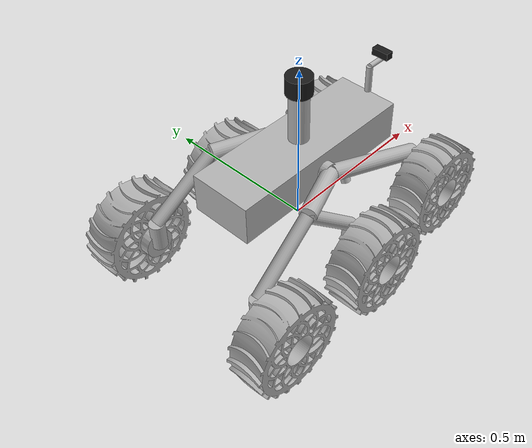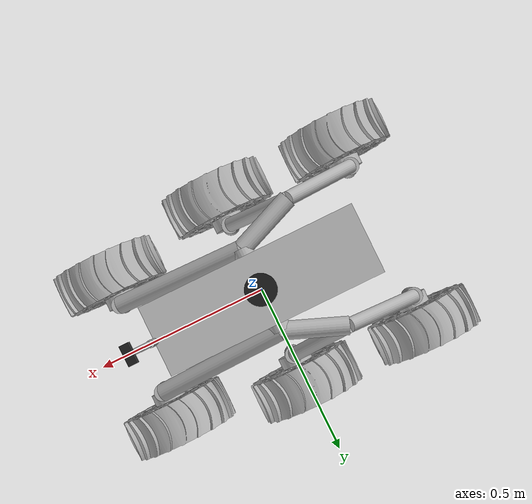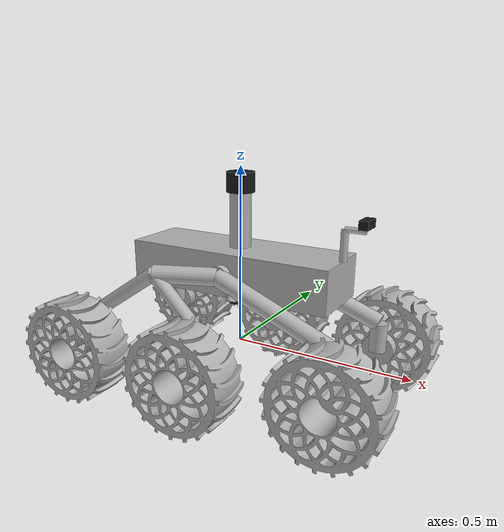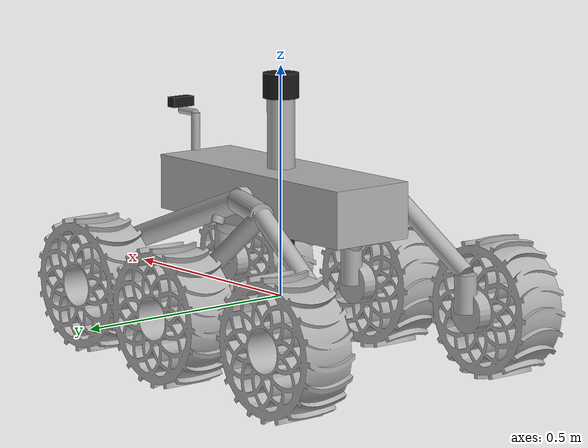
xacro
<?xml version="1.0" ?>
<robot name="ensamblajeurdf" xmlns:xacro="http://www.ros.org/wiki/xacro">

<!-- Geometric differential: a real beam and two rods.  A gearbox joint
     imposes the same relation but leaves the roll freedom unrestrained,
     and it tipped the vehicle over on the spawn drop. -->
<xacro:arg name="differential_linkage" default="false"/>

<xacro:arg name="diff_longitudinal" default="true"/>
<xacro:property name="dlong"
                value="${'$(arg diff_longitudinal)' == 'true'}"/>
<!-- el brazo del rocker solo existe si el varillaje se construye Y es
     longitudinal: en la variante transversal la barra baja inclinada y no
     hace falta subir nada -->
<xacro:property name="diff_brazo"
                value="${'$(arg diff_longitudinal)' == 'true' and
                         '$(arg differential_linkage)' == 'true'}"/>

<xacro:arg name="bogie_upper" default="0.6"/>

<xacro:arg name="bogie_drop" default="0.0"/>
<xacro:property name="bogie_drop" value="$(arg bogie_drop)"/>

<xacro:arg name="rocker_drop" default="0.299477"/>
<xacro:property name="rocker_drop" value="$(arg rocker_drop)"/>
<!-- tramo 1: la rama trasera, hasta 0.170395 -->
<xacro:property name="rk_t1" value="${min(rocker_drop, 0.170395)}"/>
<!-- tramo 2a: brazo -> junta de direccion, los 0.074002 siguientes -->
<xacro:property name="rk_t2a" value="${min(max(0.0, rocker_drop - 0.170395), 0.074002)}"/>
<!-- tramo 2b: la MANGUETA, el poste vertical de la direccion.  El ultimo en
     gastarse, porque es el que da el giro a las ruedas de las esquinas. -->
<xacro:property name="rk_t2b" value="${max(0.0, rocker_drop - 0.244397)}"/>
<xacro:property name="rk_rear" value="${1.0 - rk_t1/0.170395}"/>
<xacro:property name="rk_arm" value="${1.0 - rk_t2a/0.074002}"/>
<xacro:property name="rk_post" value="${1.0 - rk_t2b/0.137700}"/>
<xacro:property name="rk_front_z" value="${-0.256945 + rk_t1}"/>
<xacro:property name="rk_r7" value="${-0.053192*rk_rear}"/>
<xacro:property name="rk_r9" value="${-0.086551*rk_rear}"/>
<xacro:property name="rk_r11" value="${-0.030652*rk_rear}"/>
<xacro:property name="rk_p74" value="${-0.074002*rk_arm}"/>
<!-- la mangueta se queda con TODA la caida por debajo de la direccion -->
<xacro:property name="rk_p79" value="${-0.137700*rk_post}"/>
<xacro:property name="rk_p58" value="0"/>
<xacro:property name="imu_rise_per_drop" value="0.522414"/>
<xacro:property name="imu_rise_post" value="0.454931"/>
<xacro:property name="imu_rise_knuckle" value="0.439732"/>

<xacro:macro name="tubo" params="x2 y2 z2 x1:=0 y1:=0 z1:=0 r:=0.020 mat:=silver">
  <visual>
    <origin xyz="${(x1+x2)/2} ${(y1+y2)/2} ${(z1+z2)/2}"
            rpy="0 ${atan2(sqrt((x2-x1)**2+(y2-y1)**2), z2-z1)} ${atan2(y2-y1, x2-x1)}"/>
    <geometry>
      <cylinder radius="${r}"
                length="${sqrt((x2-x1)**2+(y2-y1)**2+(z2-z1)**2)}"/>
    </geometry>
    <material name="${mat}"/>
  </visual>
</xacro:macro>

<xacro:include filename="$(find rocker_bogie)/urdf/materials.xacro" />
<xacro:include filename="$(find rocker_bogie)/urdf/ensamblajeurdf.trans" />
<xacro:include filename="$(find rocker_bogie)/urdf/ensamblajeurdf.gazebo" />

<xacro:property name="mass_scale" value="0.474039"/>
<!-- Mass the differential linkage adds when it is built: 3 links x 0.05 kg.
     Subtracted from base_link so the platform total is 45.000 kg either way. -->
<xacro:property name="diff_linkage_mass"
                value="${0.15 if '$(arg differential_linkage)' == 'true' else 0.0}"/>

<link name="base_link"/>
<joint name="base_to_chassis" type="fixed">
  <origin xyz="0.244209 0.100343 ${-(0.054824 + rocker_drop)}" rpy="0 0 3.141592653589793"/>
  <parent link="base_link"/>
  <child link="chassis_link"/>
</joint>

<link name="chassis_link">
  <inertial>
    <origin xyz="0.244209 0.100344 0.574618" rpy="0 0 0"/>
    <!-- + la masa que el link del LiDAR cedio al igualarse con el husky -->
    <mass value="${(33.855 - diff_linkage_mass)*mass_scale + 4.07779*mass_scale - 0.825345 + (0.073695 + 0.04913 + 0.004913)*mass_scale - 0.025854212}"/>
    <inertia ixx="${0.393878*mass_scale}" iyy="${0.982600*mass_scale}" izz="${1.193148*mass_scale}" ixy="${0*mass_scale}" iyz="${0*mass_scale}" ixz="${2.63e-05*mass_scale}"/>
  </inertial>
  <visual>
    <origin xyz="0.244209 0.100344 0.575" rpy="0 0 0"/>
    <geometry>
      <box size="0.60 0.1926 0.12"/>
    </geometry>
    <material name="silver"/>
  </visual>
  <xacro:tubo x2="0.244209" y2="0.100343" z2="${0.5127 + rocker_drop}" x1="0.244209" y1="0.100343" z1="0.635" r="0.03"/>
  <xacro:tubo x1="-0.055791" y1="0.100343" z1="0.635" x2="-0.055791" y2="0.100343" z2="${0.4375 + rocker_drop - 0.01925}" r="0.010"/>
  <xacro:tubo x1="-0.055791" y1="0.100343" z1="${0.4375 + rocker_drop - 0.01925}" x2="-0.110091" y2="0.100343" z2="${0.4375 + rocker_drop - 0.01925}" r="0.008"/>
  <collision>
    <origin xyz="0.244209 0.100344 0.575" rpy="0 0 0"/>
    <geometry>
      <box size="0.60 0.1926 0.12"/>
    </geometry>
  </collision>
</link>

<xacro:property name="Acople_Rodamiento_1_1__m" value="${(1.39525*mass_scale) + (0.160204*mass_scale) + (0.27687*mass_scale) + (0.37221*mass_scale) + (0.37221*mass_scale) + (0.240385*mass_scale) + (3.81127*mass_scale) + (0.21391*mass_scale)}"/>
<xacro:property name="Acople_Rodamiento_1_1__x" value="${((1.39525*mass_scale)*((2.5730363188947406e-07)) + (0.160204*mass_scale)*((-0.0509408)+(-0.0828865)+(-0.026766)) + (0.27687*mass_scale)*((0.0509408)+(0.0828882)+(0.061254)) + (0.37221*mass_scale)*((-0.0509408)+(-0.048079)) + (0.37221*mass_scale)*((0.0509408)+(0.04808)) + (0.240385*mass_scale)*((-0.0509408)+(-0.0828865)+(-0.0293571)+(0)) + (3.81127*mass_scale)*((-0.0509408)+(-0.0828865)+(-0.0293571)+(0)+(0)+(0)) + (0.21391*mass_scale)*((-0.0509408)+(-0.0828865)+(-0.0293571)+(0)+(0)))/Acople_Rodamiento_1_1__m}"/>
<xacro:property name="Acople_Rodamiento_1_1__y" value="${((1.39525*mass_scale)*((-0.023282)) + (0.160204*mass_scale)*((-0.0161893)+(0.0000000)+(0)) + (0.27687*mass_scale)*((-0.0161893)+(0.0000000)+(0)) + (0.37221*mass_scale)*((-0.0161893)+(0)) + (0.37221*mass_scale)*((-0.0161893)+(0)) + (0.240385*mass_scale)*((-0.0161893)+(0.0000000)+(0.0000000)+(0)) + (3.81127*mass_scale)*((-0.0161893)+(0.0000000)+(0.0000000)+(0.0000000)+(-0.0218551)+(0.054562)) + (0.21391*mass_scale)*((-0.0161893)+(0.0000000)+(0.0000000)+(0.0000000)+(-0.004389)))/Acople_Rodamiento_1_1__m}"/>
<xacro:property name="Acople_Rodamiento_1_1__z" value="${((1.39525*mass_scale)*((-0.002333)) + (0.160204*mass_scale)*((-0.053192 + bogie_drop)+(-0.086551)+(-0.033371)) + (0.27687*mass_scale)*((-0.053192 + bogie_drop)+(-0.086551)+(-0.034916)) + (0.37221*mass_scale)*((-0.053192 + bogie_drop)+(-0.043276)) + (0.37221*mass_scale)*((-0.053192 + bogie_drop)+(-0.043276)) + (0.240385*mass_scale)*((-0.053192 + bogie_drop)+(-0.086551)+(rk_p74)+(-0.039525)) + (3.81127*mass_scale)*((-0.053192 + bogie_drop)+(-0.086551)+(rk_p74)+(rk_p79)+(rk_p58)+(-4.6319285642130973e-07)) + (0.21391*mass_scale)*((-0.053192 + bogie_drop)+(-0.086551)+(rk_p74)+(rk_p79)+(-0.047494)))/Acople_Rodamiento_1_1__m}"/>
<link name="Acople_Rodamiento_1_1">
  <inertial>
    <origin xyz="${Acople_Rodamiento_1_1__x} ${Acople_Rodamiento_1_1__y} ${Acople_Rodamiento_1_1__z}" rpy="0 0 0"/>
    <mass value="${Acople_Rodamiento_1_1__m}"/>
    <inertia ixx="${(0.001533*mass_scale) + (1.39525*mass_scale)*((((-0.023282))-Acople_Rodamiento_1_1__y)**2 + (((-0.002333))-Acople_Rodamiento_1_1__z)**2) + (0.000096*mass_scale) + (0.160204*mass_scale)*((((-0.0161893)+(0.0000000)+(0))-Acople_Rodamiento_1_1__y)**2 + (((-0.053192 + bogie_drop)+(-0.086551)+(-0.033371))-Acople_Rodamiento_1_1__z)**2) + (0.000112*mass_scale) + (0.27687*mass_scale)*((((-0.0161893)+(0.0000000)+(0))-Acople_Rodamiento_1_1__y)**2 + (((-0.053192 + bogie_drop)+(-0.086551)+(-0.034916))-Acople_Rodamiento_1_1__z)**2) + (0.000264*mass_scale) + (0.37221*mass_scale)*((((-0.0161893)+(0))-Acople_Rodamiento_1_1__y)**2 + (((-0.053192 + bogie_drop)+(-0.043276))-Acople_Rodamiento_1_1__z)**2) + (0.000264*mass_scale) + (0.37221*mass_scale)*((((-0.0161893)+(0))-Acople_Rodamiento_1_1__y)**2 + (((-0.053192 + bogie_drop)+(-0.043276))-Acople_Rodamiento_1_1__z)**2) + (0.000136*mass_scale) + (0.240385*mass_scale)*((((-0.0161893)+(0.0000000)+(0.0000000)+(0))-Acople_Rodamiento_1_1__y)**2 + (((-0.053192 + bogie_drop)+(-0.086551)+(rk_p74)+(-0.039525))-Acople_Rodamiento_1_1__z)**2) + (0.005415*mass_scale) + (3.81127*mass_scale)*((((-0.0161893)+(0.0000000)+(0.0000000)+(0.0000000)+(-0.0218551)+(0.054562))-Acople_Rodamiento_1_1__y)**2 + (((-0.053192 + bogie_drop)+(-0.086551)+(rk_p74)+(rk_p79)+(rk_p58)+(-4.6319285642130973e-07))-Acople_Rodamiento_1_1__z)**2) + (0.000208*mass_scale) + (0.21391*mass_scale)*((((-0.0161893)+(0.0000000)+(0.0000000)+(0.0000000)+(-0.004389))-Acople_Rodamiento_1_1__y)**2 + (((-0.053192 + bogie_drop)+(-0.086551)+(rk_p74)+(rk_p79)+(-0.047494))-Acople_Rodamiento_1_1__z)**2)}" iyy="${(0.002484*mass_scale) + (1.39525*mass_scale)*((((2.5730363188947406e-07))-Acople_Rodamiento_1_1__x)**2 + (((-0.002333))-Acople_Rodamiento_1_1__z)**2) + (0.000112*mass_scale) + (0.160204*mass_scale)*((((-0.0509408)+(-0.0828865)+(-0.026766))-Acople_Rodamiento_1_1__x)**2 + (((-0.053192 + bogie_drop)+(-0.086551)+(-0.033371))-Acople_Rodamiento_1_1__z)**2) + (0.000415*mass_scale) + (0.27687*mass_scale)*((((0.0509408)+(0.0828882)+(0.061254))-Acople_Rodamiento_1_1__x)**2 + (((-0.053192 + bogie_drop)+(-0.086551)+(-0.034916))-Acople_Rodamiento_1_1__z)**2) + (0.000487*mass_scale) + (0.37221*mass_scale)*((((-0.0509408)+(-0.048079))-Acople_Rodamiento_1_1__x)**2 + (((-0.053192 + bogie_drop)+(-0.043276))-Acople_Rodamiento_1_1__z)**2) + (0.000487*mass_scale) + (0.37221*mass_scale)*((((0.0509408)+(0.04808))-Acople_Rodamiento_1_1__x)**2 + (((-0.053192 + bogie_drop)+(-0.043276))-Acople_Rodamiento_1_1__z)**2) + (0.000136*mass_scale) + (0.240385*mass_scale)*((((-0.0509408)+(-0.0828865)+(-0.0293571)+(0))-Acople_Rodamiento_1_1__x)**2 + (((-0.053192 + bogie_drop)+(-0.086551)+(rk_p74)+(-0.039525))-Acople_Rodamiento_1_1__z)**2) + (0.00099*mass_scale) + (3.81127*mass_scale)*((((-0.0509408)+(-0.0828865)+(-0.0293571)+(0)+(0)+(0))-Acople_Rodamiento_1_1__x)**2 + (((-0.053192 + bogie_drop)+(-0.086551)+(rk_p74)+(rk_p79)+(rk_p58)+(-4.6319285642130973e-07))-Acople_Rodamiento_1_1__z)**2) + (0.0002*mass_scale) + (0.21391*mass_scale)*((((-0.0509408)+(-0.0828865)+(-0.0293571)+(0)+(0))-Acople_Rodamiento_1_1__x)**2 + (((-0.053192 + bogie_drop)+(-0.086551)+(rk_p74)+(rk_p79)+(-0.047494))-Acople_Rodamiento_1_1__z)**2)}" izz="${(0.001541*mass_scale) + (1.39525*mass_scale)*((((2.5730363188947406e-07))-Acople_Rodamiento_1_1__x)**2 + (((-0.023282))-Acople_Rodamiento_1_1__y)**2) + (5.5906874999999997e-05*mass_scale) + (0.160204*mass_scale)*((((-0.0509408)+(-0.0828865)+(-0.026766))-Acople_Rodamiento_1_1__x)**2 + (((-0.0161893)+(0.0000000)+(0))-Acople_Rodamiento_1_1__y)**2) + (0.000367*mass_scale) + (0.27687*mass_scale)*((((0.0509408)+(0.0828882)+(0.061254))-Acople_Rodamiento_1_1__x)**2 + (((-0.0161893)+(0.0000000)+(0))-Acople_Rodamiento_1_1__y)**2) + (0.000264*mass_scale) + (0.37221*mass_scale)*((((-0.0509408)+(-0.048079))-Acople_Rodamiento_1_1__x)**2 + (((-0.0161893)+(0))-Acople_Rodamiento_1_1__y)**2) + (0.000264*mass_scale) + (0.37221*mass_scale)*((((0.0509408)+(0.04808))-Acople_Rodamiento_1_1__x)**2 + (((-0.0161893)+(0))-Acople_Rodamiento_1_1__y)**2) + (2.396008125e-05*mass_scale) + (0.240385*mass_scale)*((((-0.0509408)+(-0.0828865)+(-0.0293571)+(0))-Acople_Rodamiento_1_1__x)**2 + (((-0.0161893)+(0.0000000)+(0.0000000)+(0))-Acople_Rodamiento_1_1__y)**2) + (0.005415*mass_scale) + (3.81127*mass_scale)*((((-0.0509408)+(-0.0828865)+(-0.0293571)+(0)+(0)+(0))-Acople_Rodamiento_1_1__x)**2 + (((-0.0161893)+(0.0000000)+(0.0000000)+(0.0000000)+(-0.0218551)+(0.054562))-Acople_Rodamiento_1_1__y)**2) + (0.000136*mass_scale) + (0.21391*mass_scale)*((((-0.0509408)+(-0.0828865)+(-0.0293571)+(0)+(0))-Acople_Rodamiento_1_1__x)**2 + (((-0.0161893)+(0.0000000)+(0.0000000)+(0.0000000)+(-0.004389))-Acople_Rodamiento_1_1__y)**2)}" ixy="${(0*mass_scale) - (1.39525*mass_scale)*(((2.5730363188947406e-07))-Acople_Rodamiento_1_1__x)*(((-0.023282))-Acople_Rodamiento_1_1__y) + (0*mass_scale) - (0.160204*mass_scale)*(((-0.0509408)+(-0.0828865)+(-0.026766))-Acople_Rodamiento_1_1__x)*(((-0.0161893)+(0.0000000)+(0))-Acople_Rodamiento_1_1__y) + (0*mass_scale) - (0.27687*mass_scale)*(((0.0509408)+(0.0828882)+(0.061254))-Acople_Rodamiento_1_1__x)*(((-0.0161893)+(0.0000000)+(0))-Acople_Rodamiento_1_1__y) + (0*mass_scale) - (0.37221*mass_scale)*(((-0.0509408)+(-0.048079))-Acople_Rodamiento_1_1__x)*(((-0.0161893)+(0))-Acople_Rodamiento_1_1__y) + (0*mass_scale) - (0.37221*mass_scale)*(((0.0509408)+(0.04808))-Acople_Rodamiento_1_1__x)*(((-0.0161893)+(0))-Acople_Rodamiento_1_1__y) + (0*mass_scale) - (0.240385*mass_scale)*(((-0.0509408)+(-0.0828865)+(-0.0293571)+(0))-Acople_Rodamiento_1_1__x)*(((-0.0161893)+(0.0000000)+(0.0000000)+(0))-Acople_Rodamiento_1_1__y) + (0*mass_scale) - (3.81127*mass_scale)*(((-0.0509408)+(-0.0828865)+(-0.0293571)+(0)+(0)+(0))-Acople_Rodamiento_1_1__x)*(((-0.0161893)+(0.0000000)+(0.0000000)+(0.0000000)+(-0.0218551)+(0.054562))-Acople_Rodamiento_1_1__y) + (0*mass_scale) - (0.21391*mass_scale)*(((-0.0509408)+(-0.0828865)+(-0.0293571)+(0)+(0))-Acople_Rodamiento_1_1__x)*(((-0.0161893)+(0.0000000)+(0.0000000)+(0.0000000)+(-0.004389))-Acople_Rodamiento_1_1__y)}" iyz="${(0*mass_scale) - (1.39525*mass_scale)*(((-0.023282))-Acople_Rodamiento_1_1__y)*(((-0.002333))-Acople_Rodamiento_1_1__z) + (0*mass_scale) - (0.160204*mass_scale)*(((-0.0161893)+(0.0000000)+(0))-Acople_Rodamiento_1_1__y)*(((-0.053192 + bogie_drop)+(-0.086551)+(-0.033371))-Acople_Rodamiento_1_1__z) + (0*mass_scale) - (0.27687*mass_scale)*(((-0.0161893)+(0.0000000)+(0))-Acople_Rodamiento_1_1__y)*(((-0.053192 + bogie_drop)+(-0.086551)+(-0.034916))-Acople_Rodamiento_1_1__z) + (0*mass_scale) - (0.37221*mass_scale)*(((-0.0161893)+(0))-Acople_Rodamiento_1_1__y)*(((-0.053192 + bogie_drop)+(-0.043276))-Acople_Rodamiento_1_1__z) + (0*mass_scale) - (0.37221*mass_scale)*(((-0.0161893)+(0))-Acople_Rodamiento_1_1__y)*(((-0.053192 + bogie_drop)+(-0.043276))-Acople_Rodamiento_1_1__z) + (0*mass_scale) - (0.240385*mass_scale)*(((-0.0161893)+(0.0000000)+(0.0000000)+(0))-Acople_Rodamiento_1_1__y)*(((-0.053192 + bogie_drop)+(-0.086551)+(rk_p74)+(-0.039525))-Acople_Rodamiento_1_1__z) + (0*mass_scale) - (3.81127*mass_scale)*(((-0.0161893)+(0.0000000)+(0.0000000)+(0.0000000)+(-0.0218551)+(0.054562))-Acople_Rodamiento_1_1__y)*(((-0.053192 + bogie_drop)+(-0.086551)+(rk_p74)+(rk_p79)+(rk_p58)+(-4.6319285642130973e-07))-Acople_Rodamiento_1_1__z) + (-7.9867125e-06*mass_scale) - (0.21391*mass_scale)*(((-0.0161893)+(0.0000000)+(0.0000000)+(0.0000000)+(-0.004389))-Acople_Rodamiento_1_1__y)*(((-0.053192 + bogie_drop)+(-0.086551)+(rk_p74)+(rk_p79)+(-0.047494))-Acople_Rodamiento_1_1__z)}" ixz="${(0*mass_scale) - (1.39525*mass_scale)*(((2.5730363188947406e-07))-Acople_Rodamiento_1_1__x)*(((-0.002333))-Acople_Rodamiento_1_1__z) + (-2.396008125e-05*mass_scale) - (0.160204*mass_scale)*(((-0.0509408)+(-0.0828865)+(-0.026766))-Acople_Rodamiento_1_1__x)*(((-0.053192 + bogie_drop)+(-0.086551)+(-0.033371))-Acople_Rodamiento_1_1__z) + (0.000096*mass_scale) - (0.27687*mass_scale)*(((0.0509408)+(0.0828882)+(0.061254))-Acople_Rodamiento_1_1__x)*(((-0.053192 + bogie_drop)+(-0.086551)+(-0.034916))-Acople_Rodamiento_1_1__z) + (-0.000224*mass_scale) - (0.37221*mass_scale)*(((-0.0509408)+(-0.048079))-Acople_Rodamiento_1_1__x)*(((-0.053192 + bogie_drop)+(-0.043276))-Acople_Rodamiento_1_1__z) + (0.000224*mass_scale) - (0.37221*mass_scale)*(((0.0509408)+(0.04808))-Acople_Rodamiento_1_1__x)*(((-0.053192 + bogie_drop)+(-0.043276))-Acople_Rodamiento_1_1__z) + (0*mass_scale) - (0.240385*mass_scale)*(((-0.0509408)+(-0.0828865)+(-0.0293571)+(0))-Acople_Rodamiento_1_1__x)*(((-0.053192 + bogie_drop)+(-0.086551)+(rk_p74)+(-0.039525))-Acople_Rodamiento_1_1__z) + (0*mass_scale) - (3.81127*mass_scale)*(((-0.0509408)+(-0.0828865)+(-0.0293571)+(0)+(0)+(0))-Acople_Rodamiento_1_1__x)*(((-0.053192 + bogie_drop)+(-0.086551)+(rk_p74)+(rk_p79)+(rk_p58)+(-4.6319285642130973e-07))-Acople_Rodamiento_1_1__z) + (0*mass_scale) - (0.21391*mass_scale)*(((-0.0509408)+(-0.0828865)+(-0.0293571)+(0)+(0))-Acople_Rodamiento_1_1__x)*(((-0.053192 + bogie_drop)+(-0.086551)+(rk_p74)+(rk_p79)+(-0.047494))-Acople_Rodamiento_1_1__z)}"/>
  </inertial>
  <xacro:tubo x1="${0}" y1="${0}" z1="${0}" x2="${(0.0509408)+(0.0828882)+(0.0707323)}" y2="${(-0.0161893)+(0.0000000)+(0.0000000)}" z2="${(-0.053192 + bogie_drop)+(-0.086551)+(rk_p74)}" r="0.020"/>
  <xacro:tubo x1="${0}" y1="${0}" z1="${0}" x2="${(-0.0509408)+(-0.0828865)+(-0.0293571)}" y2="${(-0.0161893)+(0.0000000)+(0.0000000)}" z2="${(-0.053192 + bogie_drop)+(-0.086551)+(rk_p74)}" r="0.020"/>
  <xacro:tubo x1="${(-0.0509408)+(-0.0828865)+(-0.0293571)}" y1="${(-0.0161893)+(0.0000000)+(0.0000000)}" z1="${(-0.053192 + bogie_drop)+(-0.086551)+(rk_p74)}" x2="${(-0.0509408)+(-0.0828865)+(-0.0293571)+(0)}" y2="${(-0.0161893)+(0.0000000)+(0.0000000)+(0.0000000)}" z2="${(-0.053192 + bogie_drop)+(-0.086551)+(rk_p74)+(rk_p79)}" r="0.024"/>
  <xacro:tubo x1="${(-0.0509408)+(-0.0828865)+(-0.0293571)+(0)}" y1="${(-0.0161893)+(0.0000000)+(0.0000000)+(0.0000000)}" z1="${(-0.053192 + bogie_drop)+(-0.086551)+(rk_p74)+(rk_p79)}" x2="${(-0.0509408)+(-0.0828865)+(-0.0293571)+(0)+(0)+(0)}" y2="${(-0.0161893)+(0.0000000)+(0.0000000)+(0.0000000)+(-0.0218551)+(-0.0153792)}" z2="${(-0.053192 + bogie_drop)+(-0.086551)+(rk_p74)+(rk_p79)+(rk_p58)+(0)}" r="0.045"/>
</link>

<xacro:property name="Acople_Rodamiento_2_1__m" value="${(1.39525*mass_scale) + (0.160204*mass_scale) + (0.27687*mass_scale) + (0.37221*mass_scale) + (0.37221*mass_scale) + (0.240385*mass_scale) + (3.81127*mass_scale) + (0.21391*mass_scale)}"/>
<xacro:property name="Acople_Rodamiento_2_1__x" value="${((1.39525*mass_scale)*((2.5730363188947406e-07)) + (0.160204*mass_scale)*((-0.0509408)+(-0.0828865)+(-0.026766)) + (0.27687*mass_scale)*((0.0509408)+(0.0828882)+(0.061254)) + (0.37221*mass_scale)*((-0.0509408)+(-0.048079)) + (0.37221*mass_scale)*((0.0509408)+(0.04808)) + (0.240385*mass_scale)*((-0.0509408)+(-0.0828865)+(-0.0293571)+(0)) + (3.81127*mass_scale)*((-0.0509408)+(-0.0828865)+(-0.0293571)+(0)+(0)+(0)) + (0.21391*mass_scale)*((-0.0509408)+(-0.0828865)+(-0.0293571)+(0)+(0)))/Acople_Rodamiento_2_1__m}"/>
<xacro:property name="Acople_Rodamiento_2_1__y" value="${((1.39525*mass_scale)*((0.023282)) + (0.160204*mass_scale)*((0.0161893)+(0.0000000)+(0)) + (0.27687*mass_scale)*((0.0161893)+(0.0000000)+(0)) + (0.37221*mass_scale)*((0.0161893)+(0)) + (0.37221*mass_scale)*((0.0161893)+(0)) + (0.240385*mass_scale)*((0.0161893)+(0.0000000)+(0.0000000)+(0)) + (3.81127*mass_scale)*((0.0161893)+(0.0000000)+(0.0000000)+(0.0000000)+(0.0218551)+(-0.054562)) + (0.21391*mass_scale)*((0.0161893)+(0.0000000)+(0.0000000)+(0.0000000)+(0.004389)))/Acople_Rodamiento_2_1__m}"/>
<xacro:property name="Acople_Rodamiento_2_1__z" value="${((1.39525*mass_scale)*((-0.002333)) + (0.160204*mass_scale)*((-0.053192 + bogie_drop)+(-0.086551)+(-0.033371)) + (0.27687*mass_scale)*((-0.053192 + bogie_drop)+(-0.086551)+(-0.034916)) + (0.37221*mass_scale)*((-0.053192 + bogie_drop)+(-0.043276)) + (0.37221*mass_scale)*((-0.053192 + bogie_drop)+(-0.043276)) + (0.240385*mass_scale)*((-0.053192 + bogie_drop)+(-0.086551)+(rk_p74)+(-0.039525)) + (3.81127*mass_scale)*((-0.053192 + bogie_drop)+(-0.086551)+(rk_p74)+(rk_p79)+(rk_p58)+(-4.6319285617359156e-07)) + (0.21391*mass_scale)*((-0.053192 + bogie_drop)+(-0.086551)+(rk_p74)+(rk_p79)+(-0.047494)))/Acople_Rodamiento_2_1__m}"/>
<link name="Acople_Rodamiento_2_1">
  <inertial>
    <origin xyz="${Acople_Rodamiento_2_1__x} ${Acople_Rodamiento_2_1__y} ${Acople_Rodamiento_2_1__z}" rpy="0 0 0"/>
    <mass value="${Acople_Rodamiento_2_1__m}"/>
    <inertia ixx="${(0.001533*mass_scale) + (1.39525*mass_scale)*((((0.023282))-Acople_Rodamiento_2_1__y)**2 + (((-0.002333))-Acople_Rodamiento_2_1__z)**2) + (0.000096*mass_scale) + (0.160204*mass_scale)*((((0.0161893)+(0.0000000)+(0))-Acople_Rodamiento_2_1__y)**2 + (((-0.053192 + bogie_drop)+(-0.086551)+(-0.033371))-Acople_Rodamiento_2_1__z)**2) + (0.000112*mass_scale) + (0.27687*mass_scale)*((((0.0161893)+(0.0000000)+(0))-Acople_Rodamiento_2_1__y)**2 + (((-0.053192 + bogie_drop)+(-0.086551)+(-0.034916))-Acople_Rodamiento_2_1__z)**2) + (0.000264*mass_scale) + (0.37221*mass_scale)*((((0.0161893)+(0))-Acople_Rodamiento_2_1__y)**2 + (((-0.053192 + bogie_drop)+(-0.043276))-Acople_Rodamiento_2_1__z)**2) + (0.000264*mass_scale) + (0.37221*mass_scale)*((((0.0161893)+(0))-Acople_Rodamiento_2_1__y)**2 + (((-0.053192 + bogie_drop)+(-0.043276))-Acople_Rodamiento_2_1__z)**2) + (0.000136*mass_scale) + (0.240385*mass_scale)*((((0.0161893)+(0.0000000)+(0.0000000)+(0))-Acople_Rodamiento_2_1__y)**2 + (((-0.053192 + bogie_drop)+(-0.086551)+(rk_p74)+(-0.039525))-Acople_Rodamiento_2_1__z)**2) + (0.005415*mass_scale) + (3.81127*mass_scale)*((((0.0161893)+(0.0000000)+(0.0000000)+(0.0000000)+(0.0218551)+(-0.054562))-Acople_Rodamiento_2_1__y)**2 + (((-0.053192 + bogie_drop)+(-0.086551)+(rk_p74)+(rk_p79)+(rk_p58)+(-4.6319285617359156e-07))-Acople_Rodamiento_2_1__z)**2) + (0.000208*mass_scale) + (0.21391*mass_scale)*((((0.0161893)+(0.0000000)+(0.0000000)+(0.0000000)+(0.004389))-Acople_Rodamiento_2_1__y)**2 + (((-0.053192 + bogie_drop)+(-0.086551)+(rk_p74)+(rk_p79)+(-0.047494))-Acople_Rodamiento_2_1__z)**2)}" iyy="${(0.002484*mass_scale) + (1.39525*mass_scale)*((((2.5730363188947406e-07))-Acople_Rodamiento_2_1__x)**2 + (((-0.002333))-Acople_Rodamiento_2_1__z)**2) + (0.000112*mass_scale) + (0.160204*mass_scale)*((((-0.0509408)+(-0.0828865)+(-0.026766))-Acople_Rodamiento_2_1__x)**2 + (((-0.053192 + bogie_drop)+(-0.086551)+(-0.033371))-Acople_Rodamiento_2_1__z)**2) + (0.000415*mass_scale) + (0.27687*mass_scale)*((((0.0509408)+(0.0828882)+(0.061254))-Acople_Rodamiento_2_1__x)**2 + (((-0.053192 + bogie_drop)+(-0.086551)+(-0.034916))-Acople_Rodamiento_2_1__z)**2) + (0.000487*mass_scale) + (0.37221*mass_scale)*((((-0.0509408)+(-0.048079))-Acople_Rodamiento_2_1__x)**2 + (((-0.053192 + bogie_drop)+(-0.043276))-Acople_Rodamiento_2_1__z)**2) + (0.000487*mass_scale) + (0.37221*mass_scale)*((((0.0509408)+(0.04808))-Acople_Rodamiento_2_1__x)**2 + (((-0.053192 + bogie_drop)+(-0.043276))-Acople_Rodamiento_2_1__z)**2) + (0.000136*mass_scale) + (0.240385*mass_scale)*((((-0.0509408)+(-0.0828865)+(-0.0293571)+(0))-Acople_Rodamiento_2_1__x)**2 + (((-0.053192 + bogie_drop)+(-0.086551)+(rk_p74)+(-0.039525))-Acople_Rodamiento_2_1__z)**2) + (0.00099*mass_scale) + (3.81127*mass_scale)*((((-0.0509408)+(-0.0828865)+(-0.0293571)+(0)+(0)+(0))-Acople_Rodamiento_2_1__x)**2 + (((-0.053192 + bogie_drop)+(-0.086551)+(rk_p74)+(rk_p79)+(rk_p58)+(-4.6319285617359156e-07))-Acople_Rodamiento_2_1__z)**2) + (0.0002*mass_scale) + (0.21391*mass_scale)*((((-0.0509408)+(-0.0828865)+(-0.0293571)+(0)+(0))-Acople_Rodamiento_2_1__x)**2 + (((-0.053192 + bogie_drop)+(-0.086551)+(rk_p74)+(rk_p79)+(-0.047494))-Acople_Rodamiento_2_1__z)**2)}" izz="${(0.001541*mass_scale) + (1.39525*mass_scale)*((((2.5730363188947406e-07))-Acople_Rodamiento_2_1__x)**2 + (((0.023282))-Acople_Rodamiento_2_1__y)**2) + (5.5906874999999997e-05*mass_scale) + (0.160204*mass_scale)*((((-0.0509408)+(-0.0828865)+(-0.026766))-Acople_Rodamiento_2_1__x)**2 + (((0.0161893)+(0.0000000)+(0))-Acople_Rodamiento_2_1__y)**2) + (0.000367*mass_scale) + (0.27687*mass_scale)*((((0.0509408)+(0.0828882)+(0.061254))-Acople_Rodamiento_2_1__x)**2 + (((0.0161893)+(0.0000000)+(0))-Acople_Rodamiento_2_1__y)**2) + (0.000264*mass_scale) + (0.37221*mass_scale)*((((-0.0509408)+(-0.048079))-Acople_Rodamiento_2_1__x)**2 + (((0.0161893)+(0))-Acople_Rodamiento_2_1__y)**2) + (0.000264*mass_scale) + (0.37221*mass_scale)*((((0.0509408)+(0.04808))-Acople_Rodamiento_2_1__x)**2 + (((0.0161893)+(0))-Acople_Rodamiento_2_1__y)**2) + (2.396008125e-05*mass_scale) + (0.240385*mass_scale)*((((-0.0509408)+(-0.0828865)+(-0.0293571)+(0))-Acople_Rodamiento_2_1__x)**2 + (((0.0161893)+(0.0000000)+(0.0000000)+(0))-Acople_Rodamiento_2_1__y)**2) + (0.005415*mass_scale) + (3.81127*mass_scale)*((((-0.0509408)+(-0.0828865)+(-0.0293571)+(0)+(0)+(0))-Acople_Rodamiento_2_1__x)**2 + (((0.0161893)+(0.0000000)+(0.0000000)+(0.0000000)+(0.0218551)+(-0.054562))-Acople_Rodamiento_2_1__y)**2) + (0.000136*mass_scale) + (0.21391*mass_scale)*((((-0.0509408)+(-0.0828865)+(-0.0293571)+(0)+(0))-Acople_Rodamiento_2_1__x)**2 + (((0.0161893)+(0.0000000)+(0.0000000)+(0.0000000)+(0.004389))-Acople_Rodamiento_2_1__y)**2)}" ixy="${(0*mass_scale) - (1.39525*mass_scale)*(((2.5730363188947406e-07))-Acople_Rodamiento_2_1__x)*(((0.023282))-Acople_Rodamiento_2_1__y) + (0*mass_scale) - (0.160204*mass_scale)*(((-0.0509408)+(-0.0828865)+(-0.026766))-Acople_Rodamiento_2_1__x)*(((0.0161893)+(0.0000000)+(0))-Acople_Rodamiento_2_1__y) + (0*mass_scale) - (0.27687*mass_scale)*(((0.0509408)+(0.0828882)+(0.061254))-Acople_Rodamiento_2_1__x)*(((0.0161893)+(0.0000000)+(0))-Acople_Rodamiento_2_1__y) + (0*mass_scale) - (0.37221*mass_scale)*(((-0.0509408)+(-0.048079))-Acople_Rodamiento_2_1__x)*(((0.0161893)+(0))-Acople_Rodamiento_2_1__y) + (0*mass_scale) - (0.37221*mass_scale)*(((0.0509408)+(0.04808))-Acople_Rodamiento_2_1__x)*(((0.0161893)+(0))-Acople_Rodamiento_2_1__y) + (0*mass_scale) - (0.240385*mass_scale)*(((-0.0509408)+(-0.0828865)+(-0.0293571)+(0))-Acople_Rodamiento_2_1__x)*(((0.0161893)+(0.0000000)+(0.0000000)+(0))-Acople_Rodamiento_2_1__y) + (0*mass_scale) - (3.81127*mass_scale)*(((-0.0509408)+(-0.0828865)+(-0.0293571)+(0)+(0)+(0))-Acople_Rodamiento_2_1__x)*(((0.0161893)+(0.0000000)+(0.0000000)+(0.0000000)+(0.0218551)+(-0.054562))-Acople_Rodamiento_2_1__y) + (0*mass_scale) - (0.21391*mass_scale)*(((-0.0509408)+(-0.0828865)+(-0.0293571)+(0)+(0))-Acople_Rodamiento_2_1__x)*(((0.0161893)+(0.0000000)+(0.0000000)+(0.0000000)+(0.004389))-Acople_Rodamiento_2_1__y)}" iyz="${(0*mass_scale) - (1.39525*mass_scale)*(((0.023282))-Acople_Rodamiento_2_1__y)*(((-0.002333))-Acople_Rodamiento_2_1__z) + (0*mass_scale) - (0.160204*mass_scale)*(((0.0161893)+(0.0000000)+(0))-Acople_Rodamiento_2_1__y)*(((-0.053192 + bogie_drop)+(-0.086551)+(-0.033371))-Acople_Rodamiento_2_1__z) + (0*mass_scale) - (0.27687*mass_scale)*(((0.0161893)+(0.0000000)+(0))-Acople_Rodamiento_2_1__y)*(((-0.053192 + bogie_drop)+(-0.086551)+(-0.034916))-Acople_Rodamiento_2_1__z) + (0*mass_scale) - (0.37221*mass_scale)*(((0.0161893)+(0))-Acople_Rodamiento_2_1__y)*(((-0.053192 + bogie_drop)+(-0.043276))-Acople_Rodamiento_2_1__z) + (0*mass_scale) - (0.37221*mass_scale)*(((0.0161893)+(0))-Acople_Rodamiento_2_1__y)*(((-0.053192 + bogie_drop)+(-0.043276))-Acople_Rodamiento_2_1__z) + (0*mass_scale) - (0.240385*mass_scale)*(((0.0161893)+(0.0000000)+(0.0000000)+(0))-Acople_Rodamiento_2_1__y)*(((-0.053192 + bogie_drop)+(-0.086551)+(rk_p74)+(-0.039525))-Acople_Rodamiento_2_1__z) + (0*mass_scale) - (3.81127*mass_scale)*(((0.0161893)+(0.0000000)+(0.0000000)+(0.0000000)+(0.0218551)+(-0.054562))-Acople_Rodamiento_2_1__y)*(((-0.053192 + bogie_drop)+(-0.086551)+(rk_p74)+(rk_p79)+(rk_p58)+(-4.6319285617359156e-07))-Acople_Rodamiento_2_1__z) + (7.9867125e-06*mass_scale) - (0.21391*mass_scale)*(((0.0161893)+(0.0000000)+(0.0000000)+(0.0000000)+(0.004389))-Acople_Rodamiento_2_1__y)*(((-0.053192 + bogie_drop)+(-0.086551)+(rk_p74)+(rk_p79)+(-0.047494))-Acople_Rodamiento_2_1__z)}" ixz="${(0*mass_scale) - (1.39525*mass_scale)*(((2.5730363188947406e-07))-Acople_Rodamiento_2_1__x)*(((-0.002333))-Acople_Rodamiento_2_1__z) + (-2.396008125e-05*mass_scale) - (0.160204*mass_scale)*(((-0.0509408)+(-0.0828865)+(-0.026766))-Acople_Rodamiento_2_1__x)*(((-0.053192 + bogie_drop)+(-0.086551)+(-0.033371))-Acople_Rodamiento_2_1__z) + (0.000096*mass_scale) - (0.27687*mass_scale)*(((0.0509408)+(0.0828882)+(0.061254))-Acople_Rodamiento_2_1__x)*(((-0.053192 + bogie_drop)+(-0.086551)+(-0.034916))-Acople_Rodamiento_2_1__z) + (-0.000224*mass_scale) - (0.37221*mass_scale)*(((-0.0509408)+(-0.048079))-Acople_Rodamiento_2_1__x)*(((-0.053192 + bogie_drop)+(-0.043276))-Acople_Rodamiento_2_1__z) + (0.000224*mass_scale) - (0.37221*mass_scale)*(((0.0509408)+(0.04808))-Acople_Rodamiento_2_1__x)*(((-0.053192 + bogie_drop)+(-0.043276))-Acople_Rodamiento_2_1__z) + (0*mass_scale) - (0.240385*mass_scale)*(((-0.0509408)+(-0.0828865)+(-0.0293571)+(0))-Acople_Rodamiento_2_1__x)*(((-0.053192 + bogie_drop)+(-0.086551)+(rk_p74)+(-0.039525))-Acople_Rodamiento_2_1__z) + (0*mass_scale) - (3.81127*mass_scale)*(((-0.0509408)+(-0.0828865)+(-0.0293571)+(0)+(0)+(0))-Acople_Rodamiento_2_1__x)*(((-0.053192 + bogie_drop)+(-0.086551)+(rk_p74)+(rk_p79)+(rk_p58)+(-4.6319285617359156e-07))-Acople_Rodamiento_2_1__z) + (0*mass_scale) - (0.21391*mass_scale)*(((-0.0509408)+(-0.0828865)+(-0.0293571)+(0)+(0))-Acople_Rodamiento_2_1__x)*(((-0.053192 + bogie_drop)+(-0.086551)+(rk_p74)+(rk_p79)+(-0.047494))-Acople_Rodamiento_2_1__z)}"/>
  </inertial>
  <xacro:tubo x1="${0}" y1="${0}" z1="${0}" x2="${(0.0509408)+(0.0828882)+(0.0707323)}" y2="${(0.0161893)+(0.0000000)+(0.0000000)}" z2="${(-0.053192 + bogie_drop)+(-0.086551)+(rk_p74)}" r="0.020"/>
  <xacro:tubo x1="${0}" y1="${0}" z1="${0}" x2="${(-0.0509408)+(-0.0828865)+(-0.0293571)}" y2="${(0.0161893)+(0.0000000)+(0.0000000)}" z2="${(-0.053192 + bogie_drop)+(-0.086551)+(rk_p74)}" r="0.020"/>
  <xacro:tubo x1="${(-0.0509408)+(-0.0828865)+(-0.0293571)}" y1="${(0.0161893)+(0.0000000)+(0.0000000)}" z1="${(-0.053192 + bogie_drop)+(-0.086551)+(rk_p74)}" x2="${(-0.0509408)+(-0.0828865)+(-0.0293571)+(0)}" y2="${(0.0161893)+(0.0000000)+(0.0000000)+(0.0000000)}" z2="${(-0.053192 + bogie_drop)+(-0.086551)+(rk_p74)+(rk_p79)}" r="0.024"/>
  <xacro:tubo x1="${(-0.0509408)+(-0.0828865)+(-0.0293571)+(0)}" y1="${(0.0161893)+(0.0000000)+(0.0000000)+(0.0000000)}" z1="${(-0.053192 + bogie_drop)+(-0.086551)+(rk_p74)+(rk_p79)}" x2="${(-0.0509408)+(-0.0828865)+(-0.0293571)+(0)+(0)+(0)}" y2="${(0.0161893)+(0.0000000)+(0.0000000)+(0.0000000)+(0.0218551)+(0.0153792)}" z2="${(-0.053192 + bogie_drop)+(-0.086551)+(rk_p74)+(rk_p79)+(rk_p58)+(0)}" r="0.045"/>
</link>

<xacro:property name="BarraRuedas_1_1__m" value="${(0.240385*mass_scale) + (3.81127*mass_scale) + (0.21391*mass_scale)}"/>
<xacro:property name="BarraRuedas_1_1__x" value="${((0.240385*mass_scale)*((-5.1460726387724e-07)) + (3.81127*mass_scale)*((0)+(0)+(-5.146072487797164e-07)) + (0.21391*mass_scale)*((0)+(-5.146072897081591e-07)))/BarraRuedas_1_1__m}"/>
<xacro:property name="BarraRuedas_1_1__y" value="${((0.240385*mass_scale)*((0)) + (3.81127*mass_scale)*((0.0000000)+(-0.0218551)+(0.054562)) + (0.21391*mass_scale)*((0.0000000)+(-0.004389)))/BarraRuedas_1_1__m}"/>
<xacro:property name="BarraRuedas_1_1__z" value="${((0.240385*mass_scale)*((-0.039525)) + (3.81127*mass_scale)*((rk_p79)+(rk_p58)+(-4.63192856651334e-07)) + (0.21391*mass_scale)*((rk_p79)+(-0.047494)))/BarraRuedas_1_1__m}"/>
<link name="BarraRuedas_1_1">
  <inertial>
    <origin xyz="${BarraRuedas_1_1__x} ${BarraRuedas_1_1__y} ${BarraRuedas_1_1__z}" rpy="0 0 0"/>
    <mass value="${BarraRuedas_1_1__m}"/>
    <inertia ixx="${(0.000136*mass_scale) + (0.240385*mass_scale)*((((0))-BarraRuedas_1_1__y)**2 + (((-0.039525))-BarraRuedas_1_1__z)**2) + (0.005415*mass_scale) + (3.81127*mass_scale)*((((0.0000000)+(-0.0218551)+(0.054562))-BarraRuedas_1_1__y)**2 + (((rk_p79)+(rk_p58)+(-4.63192856651334e-07))-BarraRuedas_1_1__z)**2) + (0.000208*mass_scale) + (0.21391*mass_scale)*((((0.0000000)+(-0.004389))-BarraRuedas_1_1__y)**2 + (((rk_p79)+(-0.047494))-BarraRuedas_1_1__z)**2)}" iyy="${(0.000136*mass_scale) + (0.240385*mass_scale)*((((-5.1460726387724e-07))-BarraRuedas_1_1__x)**2 + (((-0.039525))-BarraRuedas_1_1__z)**2) + (0.00099*mass_scale) + (3.81127*mass_scale)*((((0)+(0)+(-5.146072487797164e-07))-BarraRuedas_1_1__x)**2 + (((rk_p79)+(rk_p58)+(-4.63192856651334e-07))-BarraRuedas_1_1__z)**2) + (0.0002*mass_scale) + (0.21391*mass_scale)*((((0)+(-5.146072897081591e-07))-BarraRuedas_1_1__x)**2 + (((rk_p79)+(-0.047494))-BarraRuedas_1_1__z)**2)}" izz="${(2.396008125e-05*mass_scale) + (0.240385*mass_scale)*((((-5.1460726387724e-07))-BarraRuedas_1_1__x)**2 + (((0))-BarraRuedas_1_1__y)**2) + (0.005415*mass_scale) + (3.81127*mass_scale)*((((0)+(0)+(-5.146072487797164e-07))-BarraRuedas_1_1__x)**2 + (((0.0000000)+(-0.0218551)+(0.054562))-BarraRuedas_1_1__y)**2) + (0.000136*mass_scale) + (0.21391*mass_scale)*((((0)+(-5.146072897081591e-07))-BarraRuedas_1_1__x)**2 + (((0.0000000)+(-0.004389))-BarraRuedas_1_1__y)**2)}" ixy="${(0*mass_scale) - (0.240385*mass_scale)*(((-5.1460726387724e-07))-BarraRuedas_1_1__x)*(((0))-BarraRuedas_1_1__y) + (0*mass_scale) - (3.81127*mass_scale)*(((0)+(0)+(-5.146072487797164e-07))-BarraRuedas_1_1__x)*(((0.0000000)+(-0.0218551)+(0.054562))-BarraRuedas_1_1__y) + (0*mass_scale) - (0.21391*mass_scale)*(((0)+(-5.146072897081591e-07))-BarraRuedas_1_1__x)*(((0.0000000)+(-0.004389))-BarraRuedas_1_1__y)}" iyz="${(0*mass_scale) - (0.240385*mass_scale)*(((0))-BarraRuedas_1_1__y)*(((-0.039525))-BarraRuedas_1_1__z) + (0*mass_scale) - (3.81127*mass_scale)*(((0.0000000)+(-0.0218551)+(0.054562))-BarraRuedas_1_1__y)*(((rk_p79)+(rk_p58)+(-4.63192856651334e-07))-BarraRuedas_1_1__z) + (-7.9867125e-06*mass_scale) - (0.21391*mass_scale)*(((0.0000000)+(-0.004389))-BarraRuedas_1_1__y)*(((rk_p79)+(-0.047494))-BarraRuedas_1_1__z)}" ixz="${(0*mass_scale) - (0.240385*mass_scale)*(((-5.1460726387724e-07))-BarraRuedas_1_1__x)*(((-0.039525))-BarraRuedas_1_1__z) + (0*mass_scale) - (3.81127*mass_scale)*(((0)+(0)+(-5.146072487797164e-07))-BarraRuedas_1_1__x)*(((rk_p79)+(rk_p58)+(-4.63192856651334e-07))-BarraRuedas_1_1__z) + (0*mass_scale) - (0.21391*mass_scale)*(((0)+(-5.146072897081591e-07))-BarraRuedas_1_1__x)*(((rk_p79)+(-0.047494))-BarraRuedas_1_1__z)}"/>
  </inertial>
  <xacro:tubo x1="${0}" y1="${0}" z1="${0}" x2="${(0)}" y2="${(0.0000000)}" z2="${(rk_p79)}" r="0.024"/>
  <xacro:tubo x1="${(0)}" y1="${(0.0000000)}" z1="${(rk_p79)}" x2="${(0)+(0)+(0)}" y2="${(0.0000000)+(-0.0218551)+(-0.0153792)}" z2="${(rk_p79)+(rk_p58)+(0)}" r="0.045"/>
</link>

<xacro:property name="BarraRuedas_3_1__m" value="${(0.240385*mass_scale) + (3.81127*mass_scale) + (0.21391*mass_scale)}"/>
<xacro:property name="BarraRuedas_3_1__x" value="${((0.240385*mass_scale)*((5.146072640934809e-07)) + (3.81127*mass_scale)*((0)+(0)+(5.146072791910043e-07)) + (0.21391*mass_scale)*((0)+(5.146072383018786e-07)))/BarraRuedas_3_1__m}"/>
<xacro:property name="BarraRuedas_3_1__y" value="${((0.240385*mass_scale)*((0)) + (3.81127*mass_scale)*((0.0000000)+(-0.0218551)+(0.054562)) + (0.21391*mass_scale)*((0.0000000)+(-0.004389)))/BarraRuedas_3_1__m}"/>
<xacro:property name="BarraRuedas_3_1__z" value="${((0.240385*mass_scale)*((-0.039525)) + (3.81127*mass_scale)*((rk_p79)+(rk_p58)+(-4.6319285629745096e-07)) + (0.21391*mass_scale)*((rk_p79)+(-0.047494)))/BarraRuedas_3_1__m}"/>
<link name="BarraRuedas_3_1">
  <inertial>
    <origin xyz="${BarraRuedas_3_1__x} ${BarraRuedas_3_1__y} ${BarraRuedas_3_1__z}" rpy="0 0 0"/>
    <mass value="${BarraRuedas_3_1__m}"/>
    <inertia ixx="${(0.000136*mass_scale) + (0.240385*mass_scale)*((((0))-BarraRuedas_3_1__y)**2 + (((-0.039525))-BarraRuedas_3_1__z)**2) + (0.005415*mass_scale) + (3.81127*mass_scale)*((((0.0000000)+(-0.0218551)+(0.054562))-BarraRuedas_3_1__y)**2 + (((rk_p79)+(rk_p58)+(-4.6319285629745096e-07))-BarraRuedas_3_1__z)**2) + (0.000208*mass_scale) + (0.21391*mass_scale)*((((0.0000000)+(-0.004389))-BarraRuedas_3_1__y)**2 + (((rk_p79)+(-0.047494))-BarraRuedas_3_1__z)**2)}" iyy="${(0.000136*mass_scale) + (0.240385*mass_scale)*((((5.146072640934809e-07))-BarraRuedas_3_1__x)**2 + (((-0.039525))-BarraRuedas_3_1__z)**2) + (0.00099*mass_scale) + (3.81127*mass_scale)*((((0)+(0)+(5.146072791910043e-07))-BarraRuedas_3_1__x)**2 + (((rk_p79)+(rk_p58)+(-4.6319285629745096e-07))-BarraRuedas_3_1__z)**2) + (0.0002*mass_scale) + (0.21391*mass_scale)*((((0)+(5.146072383018786e-07))-BarraRuedas_3_1__x)**2 + (((rk_p79)+(-0.047494))-BarraRuedas_3_1__z)**2)}" izz="${(2.396008125e-05*mass_scale) + (0.240385*mass_scale)*((((5.146072640934809e-07))-BarraRuedas_3_1__x)**2 + (((0))-BarraRuedas_3_1__y)**2) + (0.005415*mass_scale) + (3.81127*mass_scale)*((((0)+(0)+(5.146072791910043e-07))-BarraRuedas_3_1__x)**2 + (((0.0000000)+(-0.0218551)+(0.054562))-BarraRuedas_3_1__y)**2) + (0.000136*mass_scale) + (0.21391*mass_scale)*((((0)+(5.146072383018786e-07))-BarraRuedas_3_1__x)**2 + (((0.0000000)+(-0.004389))-BarraRuedas_3_1__y)**2)}" ixy="${(0*mass_scale) - (0.240385*mass_scale)*(((5.146072640934809e-07))-BarraRuedas_3_1__x)*(((0))-BarraRuedas_3_1__y) + (0*mass_scale) - (3.81127*mass_scale)*(((0)+(0)+(5.146072791910043e-07))-BarraRuedas_3_1__x)*(((0.0000000)+(-0.0218551)+(0.054562))-BarraRuedas_3_1__y) + (0*mass_scale) - (0.21391*mass_scale)*(((0)+(5.146072383018786e-07))-BarraRuedas_3_1__x)*(((0.0000000)+(-0.004389))-BarraRuedas_3_1__y)}" iyz="${(0*mass_scale) - (0.240385*mass_scale)*(((0))-BarraRuedas_3_1__y)*(((-0.039525))-BarraRuedas_3_1__z) + (0*mass_scale) - (3.81127*mass_scale)*(((0.0000000)+(-0.0218551)+(0.054562))-BarraRuedas_3_1__y)*(((rk_p79)+(rk_p58)+(-4.6319285629745096e-07))-BarraRuedas_3_1__z) + (-7.9867125e-06*mass_scale) - (0.21391*mass_scale)*(((0.0000000)+(-0.004389))-BarraRuedas_3_1__y)*(((rk_p79)+(-0.047494))-BarraRuedas_3_1__z)}" ixz="${(0*mass_scale) - (0.240385*mass_scale)*(((5.146072640934809e-07))-BarraRuedas_3_1__x)*(((-0.039525))-BarraRuedas_3_1__z) + (0*mass_scale) - (3.81127*mass_scale)*(((0)+(0)+(5.146072791910043e-07))-BarraRuedas_3_1__x)*(((rk_p79)+(rk_p58)+(-4.6319285629745096e-07))-BarraRuedas_3_1__z) + (0*mass_scale) - (0.21391*mass_scale)*(((0)+(5.146072383018786e-07))-BarraRuedas_3_1__x)*(((rk_p79)+(-0.047494))-BarraRuedas_3_1__z)}"/>
  </inertial>
  <xacro:tubo x1="${0}" y1="${0}" z1="${0}" x2="${(0)}" y2="${(0.0000000)}" z2="${(rk_p79)}" r="0.024"/>
  <xacro:tubo x1="${(0)}" y1="${(0.0000000)}" z1="${(rk_p79)}" x2="${(0)+(0)+(0)}" y2="${(0.0000000)+(-0.0218551)+(-0.0153792)}" z2="${(rk_p79)+(rk_p58)+(0)}" r="0.045"/>
</link>

<xacro:property name="BarraRuedas_4_1__m" value="${(0.240385*mass_scale) + (3.81127*mass_scale) + (0.21391*mass_scale)}"/>
<xacro:property name="BarraRuedas_4_1__x" value="${((0.240385*mass_scale)*((-5.146072639558729e-07)) + (3.81127*mass_scale)*((0)+(0)+(-5.146072789354465e-07)) + (0.21391*mass_scale)*((0)+(-5.146072376924728e-07)))/BarraRuedas_4_1__m}"/>
<xacro:property name="BarraRuedas_4_1__y" value="${((0.240385*mass_scale)*((0)) + (3.81127*mass_scale)*((0.0000000)+(0.0218551)+(-0.054562)) + (0.21391*mass_scale)*((0.0000000)+(0.004389)))/BarraRuedas_4_1__m}"/>
<xacro:property name="BarraRuedas_4_1__z" value="${((0.240385*mass_scale)*((-0.039525)) + (3.81127*mass_scale)*((rk_p79)+(rk_p58)+(-4.6319285612050874e-07)) + (0.21391*mass_scale)*((rk_p79)+(-0.047494)))/BarraRuedas_4_1__m}"/>
<link name="BarraRuedas_4_1">
  <inertial>
    <origin xyz="${BarraRuedas_4_1__x} ${BarraRuedas_4_1__y} ${BarraRuedas_4_1__z}" rpy="0 0 0"/>
    <mass value="${BarraRuedas_4_1__m}"/>
    <inertia ixx="${(0.000136*mass_scale) + (0.240385*mass_scale)*((((0))-BarraRuedas_4_1__y)**2 + (((-0.039525))-BarraRuedas_4_1__z)**2) + (0.005415*mass_scale) + (3.81127*mass_scale)*((((0.0000000)+(0.0218551)+(-0.054562))-BarraRuedas_4_1__y)**2 + (((rk_p79)+(rk_p58)+(-4.6319285612050874e-07))-BarraRuedas_4_1__z)**2) + (0.000208*mass_scale) + (0.21391*mass_scale)*((((0.0000000)+(0.004389))-BarraRuedas_4_1__y)**2 + (((rk_p79)+(-0.047494))-BarraRuedas_4_1__z)**2)}" iyy="${(0.000136*mass_scale) + (0.240385*mass_scale)*((((-5.146072639558729e-07))-BarraRuedas_4_1__x)**2 + (((-0.039525))-BarraRuedas_4_1__z)**2) + (0.00099*mass_scale) + (3.81127*mass_scale)*((((0)+(0)+(-5.146072789354465e-07))-BarraRuedas_4_1__x)**2 + (((rk_p79)+(rk_p58)+(-4.6319285612050874e-07))-BarraRuedas_4_1__z)**2) + (0.0002*mass_scale) + (0.21391*mass_scale)*((((0)+(-5.146072376924728e-07))-BarraRuedas_4_1__x)**2 + (((rk_p79)+(-0.047494))-BarraRuedas_4_1__z)**2)}" izz="${(2.396008125e-05*mass_scale) + (0.240385*mass_scale)*((((-5.146072639558729e-07))-BarraRuedas_4_1__x)**2 + (((0))-BarraRuedas_4_1__y)**2) + (0.005415*mass_scale) + (3.81127*mass_scale)*((((0)+(0)+(-5.146072789354465e-07))-BarraRuedas_4_1__x)**2 + (((0.0000000)+(0.0218551)+(-0.054562))-BarraRuedas_4_1__y)**2) + (0.000136*mass_scale) + (0.21391*mass_scale)*((((0)+(-5.146072376924728e-07))-BarraRuedas_4_1__x)**2 + (((0.0000000)+(0.004389))-BarraRuedas_4_1__y)**2)}" ixy="${(0*mass_scale) - (0.240385*mass_scale)*(((-5.146072639558729e-07))-BarraRuedas_4_1__x)*(((0))-BarraRuedas_4_1__y) + (0*mass_scale) - (3.81127*mass_scale)*(((0)+(0)+(-5.146072789354465e-07))-BarraRuedas_4_1__x)*(((0.0000000)+(0.0218551)+(-0.054562))-BarraRuedas_4_1__y) + (0*mass_scale) - (0.21391*mass_scale)*(((0)+(-5.146072376924728e-07))-BarraRuedas_4_1__x)*(((0.0000000)+(0.004389))-BarraRuedas_4_1__y)}" iyz="${(0*mass_scale) - (0.240385*mass_scale)*(((0))-BarraRuedas_4_1__y)*(((-0.039525))-BarraRuedas_4_1__z) + (0*mass_scale) - (3.81127*mass_scale)*(((0.0000000)+(0.0218551)+(-0.054562))-BarraRuedas_4_1__y)*(((rk_p79)+(rk_p58)+(-4.6319285612050874e-07))-BarraRuedas_4_1__z) + (7.9867125e-06*mass_scale) - (0.21391*mass_scale)*(((0.0000000)+(0.004389))-BarraRuedas_4_1__y)*(((rk_p79)+(-0.047494))-BarraRuedas_4_1__z)}" ixz="${(0*mass_scale) - (0.240385*mass_scale)*(((-5.146072639558729e-07))-BarraRuedas_4_1__x)*(((-0.039525))-BarraRuedas_4_1__z) + (0*mass_scale) - (3.81127*mass_scale)*(((0)+(0)+(-5.146072789354465e-07))-BarraRuedas_4_1__x)*(((rk_p79)+(rk_p58)+(-4.6319285612050874e-07))-BarraRuedas_4_1__z) + (0*mass_scale) - (0.21391*mass_scale)*(((0)+(-5.146072376924728e-07))-BarraRuedas_4_1__x)*(((rk_p79)+(-0.047494))-BarraRuedas_4_1__z)}"/>
  </inertial>
  <xacro:tubo x1="${0}" y1="${0}" z1="${0}" x2="${(0)}" y2="${(0.0000000)}" z2="${(rk_p79)}" r="0.024"/>
  <xacro:tubo x1="${(0)}" y1="${(0.0000000)}" z1="${(rk_p79)}" x2="${(0)+(0)+(0)}" y2="${(0.0000000)+(0.0218551)+(0.0153792)}" z2="${(rk_p79)+(rk_p58)+(0)}" r="0.045"/>
</link>

<xacro:property name="BarraRuedas_6_1__m" value="${(0.240385*mass_scale) + (3.81127*mass_scale) + (0.21391*mass_scale)}"/>
<xacro:property name="BarraRuedas_6_1__x" value="${((0.240385*mass_scale)*((5.14607263778949e-07)) + (3.81127*mass_scale)*((0)+(0)+(5.146072486814256e-07)) + (0.21391*mass_scale)*((0)+(5.146072897278172e-07)))/BarraRuedas_6_1__m}"/>
<xacro:property name="BarraRuedas_6_1__y" value="${((0.240385*mass_scale)*((0)) + (3.81127*mass_scale)*((0.0000000)+(0.0218551)+(-0.054562)) + (0.21391*mass_scale)*((0.0000000)+(0.004389)))/BarraRuedas_6_1__m}"/>
<xacro:property name="BarraRuedas_6_1__z" value="${((0.240385*mass_scale)*((-0.039525)) + (3.81127*mass_scale)*((rk_p79)+(rk_p58)+(-4.631928563682277e-07)) + (0.21391*mass_scale)*((rk_p79)+(-0.047494)))/BarraRuedas_6_1__m}"/>
<link name="BarraRuedas_6_1">
  <inertial>
    <origin xyz="${BarraRuedas_6_1__x} ${BarraRuedas_6_1__y} ${BarraRuedas_6_1__z}" rpy="0 0 0"/>
    <mass value="${BarraRuedas_6_1__m}"/>
    <inertia ixx="${(0.000136*mass_scale) + (0.240385*mass_scale)*((((0))-BarraRuedas_6_1__y)**2 + (((-0.039525))-BarraRuedas_6_1__z)**2) + (0.005415*mass_scale) + (3.81127*mass_scale)*((((0.0000000)+(0.0218551)+(-0.054562))-BarraRuedas_6_1__y)**2 + (((rk_p79)+(rk_p58)+(-4.631928563682277e-07))-BarraRuedas_6_1__z)**2) + (0.000208*mass_scale) + (0.21391*mass_scale)*((((0.0000000)+(0.004389))-BarraRuedas_6_1__y)**2 + (((rk_p79)+(-0.047494))-BarraRuedas_6_1__z)**2)}" iyy="${(0.000136*mass_scale) + (0.240385*mass_scale)*((((5.14607263778949e-07))-BarraRuedas_6_1__x)**2 + (((-0.039525))-BarraRuedas_6_1__z)**2) + (0.00099*mass_scale) + (3.81127*mass_scale)*((((0)+(0)+(5.146072486814256e-07))-BarraRuedas_6_1__x)**2 + (((rk_p79)+(rk_p58)+(-4.631928563682277e-07))-BarraRuedas_6_1__z)**2) + (0.0002*mass_scale) + (0.21391*mass_scale)*((((0)+(5.146072897278172e-07))-BarraRuedas_6_1__x)**2 + (((rk_p79)+(-0.047494))-BarraRuedas_6_1__z)**2)}" izz="${(2.396008125e-05*mass_scale) + (0.240385*mass_scale)*((((5.14607263778949e-07))-BarraRuedas_6_1__x)**2 + (((0))-BarraRuedas_6_1__y)**2) + (0.005415*mass_scale) + (3.81127*mass_scale)*((((0)+(0)+(5.146072486814256e-07))-BarraRuedas_6_1__x)**2 + (((0.0000000)+(0.0218551)+(-0.054562))-BarraRuedas_6_1__y)**2) + (0.000136*mass_scale) + (0.21391*mass_scale)*((((0)+(5.146072897278172e-07))-BarraRuedas_6_1__x)**2 + (((0.0000000)+(0.004389))-BarraRuedas_6_1__y)**2)}" ixy="${(0*mass_scale) - (0.240385*mass_scale)*(((5.14607263778949e-07))-BarraRuedas_6_1__x)*(((0))-BarraRuedas_6_1__y) + (0*mass_scale) - (3.81127*mass_scale)*(((0)+(0)+(5.146072486814256e-07))-BarraRuedas_6_1__x)*(((0.0000000)+(0.0218551)+(-0.054562))-BarraRuedas_6_1__y) + (0*mass_scale) - (0.21391*mass_scale)*(((0)+(5.146072897278172e-07))-BarraRuedas_6_1__x)*(((0.0000000)+(0.004389))-BarraRuedas_6_1__y)}" iyz="${(0*mass_scale) - (0.240385*mass_scale)*(((0))-BarraRuedas_6_1__y)*(((-0.039525))-BarraRuedas_6_1__z) + (0*mass_scale) - (3.81127*mass_scale)*(((0.0000000)+(0.0218551)+(-0.054562))-BarraRuedas_6_1__y)*(((rk_p79)+(rk_p58)+(-4.631928563682277e-07))-BarraRuedas_6_1__z) + (7.9867125e-06*mass_scale) - (0.21391*mass_scale)*(((0.0000000)+(0.004389))-BarraRuedas_6_1__y)*(((rk_p79)+(-0.047494))-BarraRuedas_6_1__z)}" ixz="${(0*mass_scale) - (0.240385*mass_scale)*(((5.14607263778949e-07))-BarraRuedas_6_1__x)*(((-0.039525))-BarraRuedas_6_1__z) + (0*mass_scale) - (3.81127*mass_scale)*(((0)+(0)+(5.146072486814256e-07))-BarraRuedas_6_1__x)*(((rk_p79)+(rk_p58)+(-4.631928563682277e-07))-BarraRuedas_6_1__z) + (0*mass_scale) - (0.21391*mass_scale)*(((0)+(5.146072897278172e-07))-BarraRuedas_6_1__x)*(((rk_p79)+(-0.047494))-BarraRuedas_6_1__z)}"/>
  </inertial>
  <xacro:tubo x1="${0}" y1="${0}" z1="${0}" x2="${(0)}" y2="${(0.0000000)}" z2="${(rk_p79)}" r="0.024"/>
  <xacro:tubo x1="${(0)}" y1="${(0.0000000)}" z1="${(rk_p79)}" x2="${(0)+(0)+(0)}" y2="${(0.0000000)+(0.0218551)+(0.0153792)}" z2="${(rk_p79)+(rk_p58)+(0)}" r="0.045"/>
</link>

<link name="Rueda_2_1">
  <inertial>
    <origin xyz="-0.000463 -0.052315 0.000324" rpy="0 0 0"/>
    <mass value="${2.6357*mass_scale}"/>
    <inertia ixx="${2.6357*mass_scale*0.0065647075}" iyy="${2.6357*mass_scale*0.010952}" izz="${2.6357*mass_scale*0.0065647075}" ixy="${0.0*mass_scale}" iyz="${0.0*mass_scale}" ixz="${0.0*mass_scale}"/>
  </inertial>
  <visual>
    <origin xyz="-1.724969 0.441461 -0.147999" rpy="0 0 0"/>
    <geometry>
      <mesh filename="package://rocker_bogie/meshes/Rueda_2_1.stl" scale="0.00344186 0.00228600 0.00344186"/>
    </geometry>
    <material name="silver"/>
  </visual>
  <collision>
    <origin xyz="0 -0.052315 0" rpy="1.5707963 0 0"/>
    <geometry>
      <cylinder radius="0.148" length="0.1143"/>
    </geometry>
  </collision>
</link>

<link name="Rueda_4_1">
  <inertial>
    <origin xyz="-0.000464 -0.052315 0.000324" rpy="0 0 0"/>
    <mass value="${2.6357*mass_scale}"/>
    <inertia ixx="${2.6357*mass_scale*0.0065647075}" iyy="${2.6357*mass_scale*0.010952}" izz="${2.6357*mass_scale*0.0065647075}" ixy="${0.0*mass_scale}" iyz="${0.0*mass_scale}" ixz="${0.0*mass_scale}"/>
  </inertial>
  <visual>
    <origin xyz="-0.688372 0.441461 -0.147999" rpy="0 0 0"/>
    <geometry>
      <mesh filename="package://rocker_bogie/meshes/Rueda_4_1.stl" scale="0.00344186 0.00228600 0.00344186"/>
    </geometry>
    <material name="silver"/>
  </visual>
  <collision>
    <origin xyz="0 -0.052315 0" rpy="1.5707963 0 0"/>
    <geometry>
      <cylinder radius="0.148" length="0.1143"/>
    </geometry>
  </collision>
</link>

<link name="Rueda_6_1">
  <inertial>
    <origin xyz="-0.000466 -0.052315 0.000324" rpy="0 0 0"/>
    <mass value="${2.6357*mass_scale}"/>
    <inertia ixx="${2.6357*mass_scale*0.0065647075}" iyy="${2.6357*mass_scale*0.010952}" izz="${2.6357*mass_scale*0.0065647075}" ixy="${0.0*mass_scale}" iyz="${0.0*mass_scale}" ixz="${0.0*mass_scale}"/>
  </inertial>
  <visual>
    <origin xyz="0.348225 0.258581 -0.147999" rpy="0 0 0"/>
    <geometry>
      <mesh filename="package://rocker_bogie/meshes/Rueda_6_1.stl" scale="0.00344186 0.00228600 0.00344186"/>
    </geometry>
    <material name="silver"/>
  </visual>
  <collision>
    <origin xyz="0 -0.052315 0" rpy="1.5707963 0 0"/>
    <geometry>
      <cylinder radius="0.148" length="0.1143"/>
    </geometry>
  </collision>
</link>

<link name="Rueda_1_1">
  <inertial>
    <origin xyz="0.000463 0.052315 0.000324" rpy="0 0 0"/>
    <mass value="${2.6357*mass_scale}"/>
    <inertia ixx="${2.6357*mass_scale*0.0065647075}" iyy="${2.6357*mass_scale*0.010952}" izz="${2.6357*mass_scale*0.0065647075}" ixy="${0.0*mass_scale}" iyz="${0.0*mass_scale}" ixz="${0.0*mass_scale}"/>
  </inertial>
  <visual>
    <origin xyz="0.348225 -0.715781 -0.147999" rpy="0 0 0"/>
    <geometry>
      <mesh filename="package://rocker_bogie/meshes/Rueda_1_1.stl" scale="0.00344186 0.00228600 0.00344186"/>
    </geometry>
    <material name="silver"/>
  </visual>
  <collision>
    <origin xyz="0 0.052315 0" rpy="1.5707963 0 0"/>
    <geometry>
      <cylinder radius="0.148" length="0.1143"/>
    </geometry>
  </collision>
</link>

<link name="Rueda_3_1">
  <inertial>
    <origin xyz="0.000464 0.052315 0.000324" rpy="0 0 0"/>
    <mass value="${2.6357*mass_scale}"/>
    <inertia ixx="${2.6357*mass_scale*0.0065647075}" iyy="${2.6357*mass_scale*0.010952}" izz="${2.6357*mass_scale*0.0065647075}" ixy="${0.0*mass_scale}" iyz="${0.0*mass_scale}" ixz="${0.0*mass_scale}"/>
  </inertial>
  <visual>
    <origin xyz="-0.688372 -0.898661 -0.147999" rpy="0 0 0"/>
    <geometry>
      <mesh filename="package://rocker_bogie/meshes/Rueda_3_1.stl" scale="0.00344186 0.00228600 0.00344186"/>
    </geometry>
    <material name="silver"/>
  </visual>
  <collision>
    <origin xyz="0 0.052315 0" rpy="1.5707963 0 0"/>
    <geometry>
      <cylinder radius="0.148" length="0.1143"/>
    </geometry>
  </collision>
</link>

<link name="Rueda_5_1">
  <inertial>
    <origin xyz="0.000466 0.052315 0.000324" rpy="0 0 0"/>
    <mass value="${2.6357*mass_scale}"/>
    <inertia ixx="${2.6357*mass_scale*0.0065647075}" iyy="${2.6357*mass_scale*0.010952}" izz="${2.6357*mass_scale*0.0065647075}" ixy="${0.0*mass_scale}" iyz="${0.0*mass_scale}" ixz="${0.0*mass_scale}"/>
  </inertial>
  <visual>
    <origin xyz="-1.724969 -0.898661 -0.147999" rpy="0 0 0"/>
    <geometry>
      <mesh filename="package://rocker_bogie/meshes/Rueda_5_1.stl" scale="0.00344186 0.00228600 0.00344186"/>
    </geometry>
    <material name="silver"/>
  </visual>
  <collision>
    <origin xyz="0 0.052315 0" rpy="1.5707963 0 0"/>
    <geometry>
      <cylinder radius="0.148" length="0.1143"/>
    </geometry>
  </collision>
</link>

<xacro:property name="AcopleTuboRB_2_1__m" value="${(1.43027*mass_scale) + (1.60747*mass_scale) + (0.160204*mass_scale) + (0.27687*mass_scale) + (0.37221*mass_scale) + (1.105*mass_scale) + (0.100807*mass_scale) + (0.100807*mass_scale)}"/>
<xacro:property name="AcopleTuboRB_2_1__x" value="${((1.43027*mass_scale)*((0)) + (1.60747*mass_scale)*((0)+(0)+(0)) + (0.160204*mass_scale)*((0.0509408)+(0.0828882)+(0.027232)) + (0.27687*mass_scale)*((-0.0509408)+(-0.246072)+(-0.061254)) + (0.37221*mass_scale)*((0.0509408)+(0.048079)) + (1.105*mass_scale)*((-0.0509408)+(-0.142734)) + (0.100807*mass_scale)*((0.0509408)+(0.0828882)+(0.0293545)+(2.5730363188947406e-07)) + (0.100807*mass_scale)*((0)+(0)))/AcopleTuboRB_2_1__m}"/>
<xacro:property name="AcopleTuboRB_2_1__y" value="${((1.43027*mass_scale)*((-0.023282)) + (1.60747*mass_scale)*((0.0210457)+(0.0153792)+(-0.0042)) + (0.160204*mass_scale)*((-0.0161893)+(0.0000000)+(-0.00793)) + (0.27687*mass_scale)*((-0.0161893)+(0.0000000)+(0)) + (0.37221*mass_scale)*((-0.0161893)+(0)) + (1.105*mass_scale)*((-0.0161893)+(0)) + (0.100807*mass_scale)*((-0.0161893)+(0.0000000)+(-0.0275215)+(-0.015133)) + (0.100807*mass_scale)*((0.0210457)+(-0.015133)))/AcopleTuboRB_2_1__m}"/>
<xacro:property name="AcopleTuboRB_2_1__z" value="${((1.43027*mass_scale)*((-0.000667)) + (1.60747*mass_scale)*((0)+(0.051)+(-0.051)) + (0.160204*mass_scale)*((rk_r7)+(rk_r9)+(-0.024511)) + (0.27687*mass_scale)*((-0.053192)+(rk_front_z)+(-0.034916)) + (0.37221*mass_scale)*((rk_r7)+(-0.043275)) + (1.105*mass_scale)*((-0.053192)+(-0.128473)) + (0.100807*mass_scale)*((rk_r7)+(rk_r9)+(rk_r11)+(-2.31596427989478e-07)) + (0.100807*mass_scale)*((0)+(0)))/AcopleTuboRB_2_1__m}"/>
<xacro:property name="AcopleTuboRB_2_1__t" value="${(-0.0509408)/((-0.0509408)+(-0.246072)+(-0.0707323))}"/>
<link name="AcopleTuboRB_2_1">
  <inertial>
    <origin xyz="${AcopleTuboRB_2_1__x} ${AcopleTuboRB_2_1__y} ${AcopleTuboRB_2_1__z}" rpy="0 0 0"/>
    <mass value="${AcopleTuboRB_2_1__m}"/>
    <inertia ixx="${(0.001701*mass_scale) + (1.43027*mass_scale)*((((-0.023282))-AcopleTuboRB_2_1__y)**2 + (((-0.000667))-AcopleTuboRB_2_1__z)**2) + (0.001525*mass_scale) + (1.60747*mass_scale)*((((0.0210457)+(0.0153792)+(-0.0042))-AcopleTuboRB_2_1__y)**2 + (((0)+(0.051)+(-0.051))-AcopleTuboRB_2_1__z)**2) + (0.00008*mass_scale) + (0.160204*mass_scale)*((((-0.0161893)+(0.0000000)+(-0.00793))-AcopleTuboRB_2_1__y)**2 + (((rk_r7)+(rk_r9)+(-0.024511))-AcopleTuboRB_2_1__z)**2) + (0.000112*mass_scale) + (0.27687*mass_scale)*((((-0.0161893)+(0.0000000)+(0))-AcopleTuboRB_2_1__y)**2 + (((-0.053192)+(rk_front_z)+(-0.034916))-AcopleTuboRB_2_1__z)**2) + (0.000264*mass_scale) + (0.37221*mass_scale)*((((-0.0161893)+(0))-AcopleTuboRB_2_1__y)**2 + (((rk_r7)+(-0.043275))-AcopleTuboRB_2_1__z)**2) + (0.006166*mass_scale) + (1.105*mass_scale)*((((-0.0161893)+(0))-AcopleTuboRB_2_1__y)**2 + (((-0.053192)+(-0.128473))-AcopleTuboRB_2_1__z)**2) + (1.597336875e-05*mass_scale) + (0.100807*mass_scale)*((((-0.0161893)+(0.0000000)+(-0.0275215)+(-0.015133))-AcopleTuboRB_2_1__y)**2 + (((rk_r7)+(rk_r9)+(rk_r11)+(-2.31596427989478e-07))-AcopleTuboRB_2_1__z)**2) + (1.597336875e-05*mass_scale) + (0.100807*mass_scale)*((((0.0210457)+(-0.015133))-AcopleTuboRB_2_1__y)**2 + (((0)+(0))-AcopleTuboRB_2_1__z)**2)}" iyy="${(0.002652*mass_scale) + (1.43027*mass_scale)*((((0))-AcopleTuboRB_2_1__x)**2 + (((-0.000667))-AcopleTuboRB_2_1__z)**2) + (0.002987*mass_scale) + (1.60747*mass_scale)*((((0)+(0)+(0))-AcopleTuboRB_2_1__x)**2 + (((0)+(0.051)+(-0.051))-AcopleTuboRB_2_1__z)**2) + (0.000072*mass_scale) + (0.160204*mass_scale)*((((0.0509408)+(0.0828882)+(0.027232))-AcopleTuboRB_2_1__x)**2 + (((rk_r7)+(rk_r9)+(-0.024511))-AcopleTuboRB_2_1__z)**2) + (0.000415*mass_scale) + (0.27687*mass_scale)*((((-0.0509408)+(-0.246072)+(-0.061254))-AcopleTuboRB_2_1__x)**2 + (((-0.053192)+(rk_front_z)+(-0.034916))-AcopleTuboRB_2_1__z)**2) + (0.000487*mass_scale) + (0.37221*mass_scale)*((((0.0509408)+(0.048079))-AcopleTuboRB_2_1__x)**2 + (((rk_r7)+(-0.043275))-AcopleTuboRB_2_1__z)**2) + (0.01222*mass_scale) + (1.105*mass_scale)*((((-0.0509408)+(-0.142734))-AcopleTuboRB_2_1__x)**2 + (((-0.053192)+(-0.128473))-AcopleTuboRB_2_1__z)**2) + (7.9867125e-06*mass_scale) + (0.100807*mass_scale)*((((0.0509408)+(0.0828882)+(0.0293545)+(2.5730363188947406e-07))-AcopleTuboRB_2_1__x)**2 + (((rk_r7)+(rk_r9)+(rk_r11)+(-2.31596427989478e-07))-AcopleTuboRB_2_1__z)**2) + (7.9867125e-06*mass_scale) + (0.100807*mass_scale)*((((0)+(0))-AcopleTuboRB_2_1__x)**2 + (((0)+(0))-AcopleTuboRB_2_1__z)**2)}" izz="${(0.001549*mass_scale) + (1.43027*mass_scale)*((((0))-AcopleTuboRB_2_1__x)**2 + (((-0.023282))-AcopleTuboRB_2_1__y)**2) + (0.001525*mass_scale) + (1.60747*mass_scale)*((((0)+(0)+(0))-AcopleTuboRB_2_1__x)**2 + (((0.0210457)+(0.0153792)+(-0.0042))-AcopleTuboRB_2_1__y)**2) + (0.00008*mass_scale) + (0.160204*mass_scale)*((((0.0509408)+(0.0828882)+(0.027232))-AcopleTuboRB_2_1__x)**2 + (((-0.0161893)+(0.0000000)+(-0.00793))-AcopleTuboRB_2_1__y)**2) + (0.000367*mass_scale) + (0.27687*mass_scale)*((((-0.0509408)+(-0.246072)+(-0.061254))-AcopleTuboRB_2_1__x)**2 + (((-0.0161893)+(0.0000000)+(0))-AcopleTuboRB_2_1__y)**2) + (0.000264*mass_scale) + (0.37221*mass_scale)*((((0.0509408)+(0.048079))-AcopleTuboRB_2_1__x)**2 + (((-0.0161893)+(0))-AcopleTuboRB_2_1__y)**2) + (0.006166*mass_scale) + (1.105*mass_scale)*((((-0.0509408)+(-0.142734))-AcopleTuboRB_2_1__x)**2 + (((-0.0161893)+(0))-AcopleTuboRB_2_1__y)**2) + (1.597336875e-05*mass_scale) + (0.100807*mass_scale)*((((0.0509408)+(0.0828882)+(0.0293545)+(2.5730363188947406e-07))-AcopleTuboRB_2_1__x)**2 + (((-0.0161893)+(0.0000000)+(-0.0275215)+(-0.015133))-AcopleTuboRB_2_1__y)**2) + (1.597336875e-05*mass_scale) + (0.100807*mass_scale)*((((0)+(0))-AcopleTuboRB_2_1__x)**2 + (((0.0210457)+(-0.015133))-AcopleTuboRB_2_1__y)**2)}" ixy="${(0*mass_scale) - (1.43027*mass_scale)*(((0))-AcopleTuboRB_2_1__x)*(((-0.023282))-AcopleTuboRB_2_1__y) + (0*mass_scale) - (1.60747*mass_scale)*(((0)+(0)+(0))-AcopleTuboRB_2_1__x)*(((0.0210457)+(0.0153792)+(-0.0042))-AcopleTuboRB_2_1__y) + (7.9867125e-06*mass_scale) - (0.160204*mass_scale)*(((0.0509408)+(0.0828882)+(0.027232))-AcopleTuboRB_2_1__x)*(((-0.0161893)+(0.0000000)+(-0.00793))-AcopleTuboRB_2_1__y) + (0*mass_scale) - (0.27687*mass_scale)*(((-0.0509408)+(-0.246072)+(-0.061254))-AcopleTuboRB_2_1__x)*(((-0.0161893)+(0.0000000)+(0))-AcopleTuboRB_2_1__y) + (0*mass_scale) - (0.37221*mass_scale)*(((0.0509408)+(0.048079))-AcopleTuboRB_2_1__x)*(((-0.0161893)+(0))-AcopleTuboRB_2_1__y) + (0*mass_scale) - (1.105*mass_scale)*(((-0.0509408)+(-0.142734))-AcopleTuboRB_2_1__x)*(((-0.0161893)+(0))-AcopleTuboRB_2_1__y) + (0*mass_scale) - (0.100807*mass_scale)*(((0.0509408)+(0.0828882)+(0.0293545)+(2.5730363188947406e-07))-AcopleTuboRB_2_1__x)*(((-0.0161893)+(0.0000000)+(-0.0275215)+(-0.015133))-AcopleTuboRB_2_1__y) + (0*mass_scale) - (0.100807*mass_scale)*(((0)+(0))-AcopleTuboRB_2_1__x)*(((0.0210457)+(-0.015133))-AcopleTuboRB_2_1__y)}" iyz="${(0*mass_scale) - (1.43027*mass_scale)*(((-0.023282))-AcopleTuboRB_2_1__y)*(((-0.000667))-AcopleTuboRB_2_1__z) + (0*mass_scale) - (1.60747*mass_scale)*(((0.0210457)+(0.0153792)+(-0.0042))-AcopleTuboRB_2_1__y)*(((0)+(0.051)+(-0.051))-AcopleTuboRB_2_1__z) + (-7.9867125e-06*mass_scale) - (0.160204*mass_scale)*(((-0.0161893)+(0.0000000)+(-0.00793))-AcopleTuboRB_2_1__y)*(((rk_r7)+(rk_r9)+(-0.024511))-AcopleTuboRB_2_1__z) + (0*mass_scale) - (0.27687*mass_scale)*(((-0.0161893)+(0.0000000)+(0))-AcopleTuboRB_2_1__y)*(((-0.053192)+(rk_front_z)+(-0.034916))-AcopleTuboRB_2_1__z) + (0*mass_scale) - (0.37221*mass_scale)*(((-0.0161893)+(0))-AcopleTuboRB_2_1__y)*(((rk_r7)+(-0.043275))-AcopleTuboRB_2_1__z) + (0*mass_scale) - (1.105*mass_scale)*(((-0.0161893)+(0))-AcopleTuboRB_2_1__y)*(((-0.053192)+(-0.128473))-AcopleTuboRB_2_1__z) + (0*mass_scale) - (0.100807*mass_scale)*(((-0.0161893)+(0.0000000)+(-0.0275215)+(-0.015133))-AcopleTuboRB_2_1__y)*(((rk_r7)+(rk_r9)+(rk_r11)+(-2.31596427989478e-07))-AcopleTuboRB_2_1__z) + (0*mass_scale) - (0.100807*mass_scale)*(((0.0210457)+(-0.015133))-AcopleTuboRB_2_1__y)*(((0)+(0))-AcopleTuboRB_2_1__z)}" ixz="${(0*mass_scale) - (1.43027*mass_scale)*(((0))-AcopleTuboRB_2_1__x)*(((-0.000667))-AcopleTuboRB_2_1__z) + (0*mass_scale) - (1.60747*mass_scale)*(((0)+(0)+(0))-AcopleTuboRB_2_1__x)*(((0)+(0.051)+(-0.051))-AcopleTuboRB_2_1__z) + (1.597336875e-05*mass_scale) - (0.160204*mass_scale)*(((0.0509408)+(0.0828882)+(0.027232))-AcopleTuboRB_2_1__x)*(((rk_r7)+(rk_r9)+(-0.024511))-AcopleTuboRB_2_1__z) + (-0.000096*mass_scale) - (0.27687*mass_scale)*(((-0.0509408)+(-0.246072)+(-0.061254))-AcopleTuboRB_2_1__x)*(((-0.053192)+(rk_front_z)+(-0.034916))-AcopleTuboRB_2_1__z) + (0.000224*mass_scale) - (0.37221*mass_scale)*(((0.0509408)+(0.048079))-AcopleTuboRB_2_1__x)*(((rk_r7)+(-0.043275))-AcopleTuboRB_2_1__z) + (-0.006054*mass_scale) - (1.105*mass_scale)*(((-0.0509408)+(-0.142734))-AcopleTuboRB_2_1__x)*(((-0.053192)+(-0.128473))-AcopleTuboRB_2_1__z) + (0*mass_scale) - (0.100807*mass_scale)*(((0.0509408)+(0.0828882)+(0.0293545)+(2.5730363188947406e-07))-AcopleTuboRB_2_1__x)*(((rk_r7)+(rk_r9)+(rk_r11)+(-2.31596427989478e-07))-AcopleTuboRB_2_1__z) + (0*mass_scale) - (0.100807*mass_scale)*(((0)+(0))-AcopleTuboRB_2_1__x)*(((0)+(0))-AcopleTuboRB_2_1__z)}"/>
  </inertial>
  <xacro:tubo x1="${0}" y1="${0}" z1="${0}" x2="${0}" y2="${0.0210457}" z2="${0}" r="0.028"/>
  <xacro:tubo x1="${0}" y1="${0}" z1="${0}" x2="${(0.0509408)+(0.0828882)+(0.0293545)+(0)}" y2="${(-0.0161893)+(0.0000000)+(-0.0275215)+(-0.0210457)}" z2="${(rk_r7)+(rk_r9)+(rk_r11)+(-bogie_drop)}" r="0.025"/>
  <xacro:tubo x1="${0}" y1="${0}" z1="${0}" x2="${(-0.0509408)+(-0.246072)+(-0.0707323)}" y2="${(-0.0161893)+(0.0000000)+(0.0000000)}" z2="${(-0.053192)+(rk_front_z)+(rk_p74)}" r="0.025"/>
  <xacro:tubo x1="${((-0.0509408)+(-0.246072)+(-0.0707323))*AcopleTuboRB_2_1__t}" y1="${((-0.0161893)+(0.0000000)+(0.0000000))*AcopleTuboRB_2_1__t}" z1="${((-0.053192)+(rk_front_z)+(rk_p74))*AcopleTuboRB_2_1__t}" x2="${-0.0509408}" y2="${-0.0161893}" z2="${-0.053192}" r="0.014"/>
  <xacro:if value="${diff_brazo}">
    <xacro:tubo x1="${0}" y1="${-0.0161893}" z1="${0}"
                x2="${0}" y2="${-0.0161893}" z2="${0.096808}" r="0.012"/>
  </xacro:if>
</link>

<xacro:property name="AcopleTuboRB_1_1__m" value="${(1.43027*mass_scale) + (1.60747*mass_scale) + (0.160204*mass_scale) + (0.27687*mass_scale) + (0.37221*mass_scale) + (1.105*mass_scale) + (0.100807*mass_scale) + (0.100807*mass_scale)}"/>
<xacro:property name="AcopleTuboRB_1_1__x" value="${((1.43027*mass_scale)*((0)) + (1.60747*mass_scale)*((0)+(0)+(0)) + (0.160204*mass_scale)*((0.0509408)+(0.0828882)+(0.027232)) + (0.27687*mass_scale)*((-0.0509408)+(-0.246072)+(-0.061254)) + (0.37221*mass_scale)*((0.0509408)+(0.048079)) + (1.105*mass_scale)*((-0.0509408)+(-0.142734)) + (0.100807*mass_scale)*((0.0509408)+(0.0828882)+(0.0293545)+(2.5730363188947406e-07)) + (0.100807*mass_scale)*((0)+(0)))/AcopleTuboRB_1_1__m}"/>
<xacro:property name="AcopleTuboRB_1_1__y" value="${((1.43027*mass_scale)*((0.023282)) + (1.60747*mass_scale)*((-0.0210457)+(-0.0153792)+(0.0042)) + (0.160204*mass_scale)*((0.0161893)+(0.0000000)+(0.00793)) + (0.27687*mass_scale)*((0.0161893)+(0.0000000)+(0)) + (0.37221*mass_scale)*((0.0161893)+(0)) + (1.105*mass_scale)*((0.0161893)+(0)) + (0.100807*mass_scale)*((0.0161893)+(0.0000000)+(0.0275215)+(0.015133)) + (0.100807*mass_scale)*((-0.0210457)+(0.015133)))/AcopleTuboRB_1_1__m}"/>
<xacro:property name="AcopleTuboRB_1_1__z" value="${((1.43027*mass_scale)*((-0.000667)) + (1.60747*mass_scale)*((0)+(0.051)+(-0.051)) + (0.160204*mass_scale)*((rk_r7)+(rk_r9)+(-0.024511)) + (0.27687*mass_scale)*((-0.053192)+(rk_front_z)+(-0.034916)) + (0.37221*mass_scale)*((rk_r7)+(-0.043275)) + (1.105*mass_scale)*((-0.053192)+(-0.128473)) + (0.100807*mass_scale)*((rk_r7)+(rk_r9)+(rk_r11)+(-2.31596427989478e-07)) + (0.100807*mass_scale)*((0)+(0)))/AcopleTuboRB_1_1__m}"/>
<xacro:property name="AcopleTuboRB_1_1__t" value="${(-0.0509408)/((-0.0509408)+(-0.246072)+(-0.0707323))}"/>
<link name="AcopleTuboRB_1_1">
  <inertial>
    <origin xyz="${AcopleTuboRB_1_1__x} ${AcopleTuboRB_1_1__y} ${AcopleTuboRB_1_1__z}" rpy="0 0 0"/>
    <mass value="${AcopleTuboRB_1_1__m}"/>
    <inertia ixx="${(0.001701*mass_scale) + (1.43027*mass_scale)*((((0.023282))-AcopleTuboRB_1_1__y)**2 + (((-0.000667))-AcopleTuboRB_1_1__z)**2) + (0.001525*mass_scale) + (1.60747*mass_scale)*((((-0.0210457)+(-0.0153792)+(0.0042))-AcopleTuboRB_1_1__y)**2 + (((0)+(0.051)+(-0.051))-AcopleTuboRB_1_1__z)**2) + (0.00008*mass_scale) + (0.160204*mass_scale)*((((0.0161893)+(0.0000000)+(0.00793))-AcopleTuboRB_1_1__y)**2 + (((rk_r7)+(rk_r9)+(-0.024511))-AcopleTuboRB_1_1__z)**2) + (0.000112*mass_scale) + (0.27687*mass_scale)*((((0.0161893)+(0.0000000)+(0))-AcopleTuboRB_1_1__y)**2 + (((-0.053192)+(rk_front_z)+(-0.034916))-AcopleTuboRB_1_1__z)**2) + (0.000264*mass_scale) + (0.37221*mass_scale)*((((0.0161893)+(0))-AcopleTuboRB_1_1__y)**2 + (((rk_r7)+(-0.043275))-AcopleTuboRB_1_1__z)**2) + (0.006166*mass_scale) + (1.105*mass_scale)*((((0.0161893)+(0))-AcopleTuboRB_1_1__y)**2 + (((-0.053192)+(-0.128473))-AcopleTuboRB_1_1__z)**2) + (1.597336875e-05*mass_scale) + (0.100807*mass_scale)*((((0.0161893)+(0.0000000)+(0.0275215)+(0.015133))-AcopleTuboRB_1_1__y)**2 + (((rk_r7)+(rk_r9)+(rk_r11)+(-2.31596427989478e-07))-AcopleTuboRB_1_1__z)**2) + (1.597336875e-05*mass_scale) + (0.100807*mass_scale)*((((-0.0210457)+(0.015133))-AcopleTuboRB_1_1__y)**2 + (((0)+(0))-AcopleTuboRB_1_1__z)**2)}" iyy="${(0.002652*mass_scale) + (1.43027*mass_scale)*((((0))-AcopleTuboRB_1_1__x)**2 + (((-0.000667))-AcopleTuboRB_1_1__z)**2) + (0.002987*mass_scale) + (1.60747*mass_scale)*((((0)+(0)+(0))-AcopleTuboRB_1_1__x)**2 + (((0)+(0.051)+(-0.051))-AcopleTuboRB_1_1__z)**2) + (0.000072*mass_scale) + (0.160204*mass_scale)*((((0.0509408)+(0.0828882)+(0.027232))-AcopleTuboRB_1_1__x)**2 + (((rk_r7)+(rk_r9)+(-0.024511))-AcopleTuboRB_1_1__z)**2) + (0.000415*mass_scale) + (0.27687*mass_scale)*((((-0.0509408)+(-0.246072)+(-0.061254))-AcopleTuboRB_1_1__x)**2 + (((-0.053192)+(rk_front_z)+(-0.034916))-AcopleTuboRB_1_1__z)**2) + (0.000487*mass_scale) + (0.37221*mass_scale)*((((0.0509408)+(0.048079))-AcopleTuboRB_1_1__x)**2 + (((rk_r7)+(-0.043275))-AcopleTuboRB_1_1__z)**2) + (0.01222*mass_scale) + (1.105*mass_scale)*((((-0.0509408)+(-0.142734))-AcopleTuboRB_1_1__x)**2 + (((-0.053192)+(-0.128473))-AcopleTuboRB_1_1__z)**2) + (7.9867125e-06*mass_scale) + (0.100807*mass_scale)*((((0.0509408)+(0.0828882)+(0.0293545)+(2.5730363188947406e-07))-AcopleTuboRB_1_1__x)**2 + (((rk_r7)+(rk_r9)+(rk_r11)+(-2.31596427989478e-07))-AcopleTuboRB_1_1__z)**2) + (7.9867125e-06*mass_scale) + (0.100807*mass_scale)*((((0)+(0))-AcopleTuboRB_1_1__x)**2 + (((0)+(0))-AcopleTuboRB_1_1__z)**2)}" izz="${(0.001549*mass_scale) + (1.43027*mass_scale)*((((0))-AcopleTuboRB_1_1__x)**2 + (((0.023282))-AcopleTuboRB_1_1__y)**2) + (0.001525*mass_scale) + (1.60747*mass_scale)*((((0)+(0)+(0))-AcopleTuboRB_1_1__x)**2 + (((-0.0210457)+(-0.0153792)+(0.0042))-AcopleTuboRB_1_1__y)**2) + (0.00008*mass_scale) + (0.160204*mass_scale)*((((0.0509408)+(0.0828882)+(0.027232))-AcopleTuboRB_1_1__x)**2 + (((0.0161893)+(0.0000000)+(0.00793))-AcopleTuboRB_1_1__y)**2) + (0.000367*mass_scale) + (0.27687*mass_scale)*((((-0.0509408)+(-0.246072)+(-0.061254))-AcopleTuboRB_1_1__x)**2 + (((0.0161893)+(0.0000000)+(0))-AcopleTuboRB_1_1__y)**2) + (0.000264*mass_scale) + (0.37221*mass_scale)*((((0.0509408)+(0.048079))-AcopleTuboRB_1_1__x)**2 + (((0.0161893)+(0))-AcopleTuboRB_1_1__y)**2) + (0.006166*mass_scale) + (1.105*mass_scale)*((((-0.0509408)+(-0.142734))-AcopleTuboRB_1_1__x)**2 + (((0.0161893)+(0))-AcopleTuboRB_1_1__y)**2) + (1.597336875e-05*mass_scale) + (0.100807*mass_scale)*((((0.0509408)+(0.0828882)+(0.0293545)+(2.5730363188947406e-07))-AcopleTuboRB_1_1__x)**2 + (((0.0161893)+(0.0000000)+(0.0275215)+(0.015133))-AcopleTuboRB_1_1__y)**2) + (1.597336875e-05*mass_scale) + (0.100807*mass_scale)*((((0)+(0))-AcopleTuboRB_1_1__x)**2 + (((-0.0210457)+(0.015133))-AcopleTuboRB_1_1__y)**2)}" ixy="${(0*mass_scale) - (1.43027*mass_scale)*(((0))-AcopleTuboRB_1_1__x)*(((0.023282))-AcopleTuboRB_1_1__y) + (0*mass_scale) - (1.60747*mass_scale)*(((0)+(0)+(0))-AcopleTuboRB_1_1__x)*(((-0.0210457)+(-0.0153792)+(0.0042))-AcopleTuboRB_1_1__y) + (-7.9867125e-06*mass_scale) - (0.160204*mass_scale)*(((0.0509408)+(0.0828882)+(0.027232))-AcopleTuboRB_1_1__x)*(((0.0161893)+(0.0000000)+(0.00793))-AcopleTuboRB_1_1__y) + (0*mass_scale) - (0.27687*mass_scale)*(((-0.0509408)+(-0.246072)+(-0.061254))-AcopleTuboRB_1_1__x)*(((0.0161893)+(0.0000000)+(0))-AcopleTuboRB_1_1__y) + (0*mass_scale) - (0.37221*mass_scale)*(((0.0509408)+(0.048079))-AcopleTuboRB_1_1__x)*(((0.0161893)+(0))-AcopleTuboRB_1_1__y) + (0*mass_scale) - (1.105*mass_scale)*(((-0.0509408)+(-0.142734))-AcopleTuboRB_1_1__x)*(((0.0161893)+(0))-AcopleTuboRB_1_1__y) + (0*mass_scale) - (0.100807*mass_scale)*(((0.0509408)+(0.0828882)+(0.0293545)+(2.5730363188947406e-07))-AcopleTuboRB_1_1__x)*(((0.0161893)+(0.0000000)+(0.0275215)+(0.015133))-AcopleTuboRB_1_1__y) + (0*mass_scale) - (0.100807*mass_scale)*(((0)+(0))-AcopleTuboRB_1_1__x)*(((-0.0210457)+(0.015133))-AcopleTuboRB_1_1__y)}" iyz="${(0*mass_scale) - (1.43027*mass_scale)*(((0.023282))-AcopleTuboRB_1_1__y)*(((-0.000667))-AcopleTuboRB_1_1__z) + (0*mass_scale) - (1.60747*mass_scale)*(((-0.0210457)+(-0.0153792)+(0.0042))-AcopleTuboRB_1_1__y)*(((0)+(0.051)+(-0.051))-AcopleTuboRB_1_1__z) + (7.9867125e-06*mass_scale) - (0.160204*mass_scale)*(((0.0161893)+(0.0000000)+(0.00793))-AcopleTuboRB_1_1__y)*(((rk_r7)+(rk_r9)+(-0.024511))-AcopleTuboRB_1_1__z) + (0*mass_scale) - (0.27687*mass_scale)*(((0.0161893)+(0.0000000)+(0))-AcopleTuboRB_1_1__y)*(((-0.053192)+(rk_front_z)+(-0.034916))-AcopleTuboRB_1_1__z) + (0*mass_scale) - (0.37221*mass_scale)*(((0.0161893)+(0))-AcopleTuboRB_1_1__y)*(((rk_r7)+(-0.043275))-AcopleTuboRB_1_1__z) + (0*mass_scale) - (1.105*mass_scale)*(((0.0161893)+(0))-AcopleTuboRB_1_1__y)*(((-0.053192)+(-0.128473))-AcopleTuboRB_1_1__z) + (0*mass_scale) - (0.100807*mass_scale)*(((0.0161893)+(0.0000000)+(0.0275215)+(0.015133))-AcopleTuboRB_1_1__y)*(((rk_r7)+(rk_r9)+(rk_r11)+(-2.31596427989478e-07))-AcopleTuboRB_1_1__z) + (0*mass_scale) - (0.100807*mass_scale)*(((-0.0210457)+(0.015133))-AcopleTuboRB_1_1__y)*(((0)+(0))-AcopleTuboRB_1_1__z)}" ixz="${(0*mass_scale) - (1.43027*mass_scale)*(((0))-AcopleTuboRB_1_1__x)*(((-0.000667))-AcopleTuboRB_1_1__z) + (0*mass_scale) - (1.60747*mass_scale)*(((0)+(0)+(0))-AcopleTuboRB_1_1__x)*(((0)+(0.051)+(-0.051))-AcopleTuboRB_1_1__z) + (1.597336875e-05*mass_scale) - (0.160204*mass_scale)*(((0.0509408)+(0.0828882)+(0.027232))-AcopleTuboRB_1_1__x)*(((rk_r7)+(rk_r9)+(-0.024511))-AcopleTuboRB_1_1__z) + (-0.000096*mass_scale) - (0.27687*mass_scale)*(((-0.0509408)+(-0.246072)+(-0.061254))-AcopleTuboRB_1_1__x)*(((-0.053192)+(rk_front_z)+(-0.034916))-AcopleTuboRB_1_1__z) + (0.000224*mass_scale) - (0.37221*mass_scale)*(((0.0509408)+(0.048079))-AcopleTuboRB_1_1__x)*(((rk_r7)+(-0.043275))-AcopleTuboRB_1_1__z) + (-0.006054*mass_scale) - (1.105*mass_scale)*(((-0.0509408)+(-0.142734))-AcopleTuboRB_1_1__x)*(((-0.053192)+(-0.128473))-AcopleTuboRB_1_1__z) + (0*mass_scale) - (0.100807*mass_scale)*(((0.0509408)+(0.0828882)+(0.0293545)+(2.5730363188947406e-07))-AcopleTuboRB_1_1__x)*(((rk_r7)+(rk_r9)+(rk_r11)+(-2.31596427989478e-07))-AcopleTuboRB_1_1__z) + (0*mass_scale) - (0.100807*mass_scale)*(((0)+(0))-AcopleTuboRB_1_1__x)*(((0)+(0))-AcopleTuboRB_1_1__z)}"/>
  </inertial>
  <xacro:tubo x1="${0}" y1="${0}" z1="${0}" x2="${0}" y2="${-0.0210457}" z2="${0}" r="0.028"/>
  <xacro:tubo x1="${0}" y1="${0}" z1="${0}" x2="${(0.0509408)+(0.0828882)+(0.0293545)+(0)}" y2="${(0.0161893)+(0.0000000)+(0.0275215)+(0.0210457)}" z2="${(rk_r7)+(rk_r9)+(rk_r11)+(-bogie_drop)}" r="0.025"/>
  <xacro:tubo x1="${0}" y1="${0}" z1="${0}" x2="${(-0.0509408)+(-0.246072)+(-0.0707323)}" y2="${(0.0161893)+(0.0000000)+(0.0000000)}" z2="${(-0.053192)+(rk_front_z)+(rk_p74)}" r="0.025"/>
  <xacro:tubo x1="${((-0.0509408)+(-0.246072)+(-0.0707323))*AcopleTuboRB_1_1__t}" y1="${((0.0161893)+(0.0000000)+(0.0000000))*AcopleTuboRB_1_1__t}" z1="${((-0.053192)+(rk_front_z)+(rk_p74))*AcopleTuboRB_1_1__t}" x2="${-0.0509408}" y2="${0.0161893}" z2="${-0.053192}" r="0.014"/>
  <xacro:if value="${diff_brazo}">
    <xacro:tubo x1="${0}" y1="${0.0161893}" z1="${0}"
                x2="${0}" y2="${0.0161893}" z2="${0.096808}" r="0.012"/>
  </xacro:if>
</link>

<!-- ================= ROCKER PIVOTS (passive suspension) ================= -->

<!-- ================= SUSPENSION DAMPING ================= -->

<joint name="rocker_pivot_right" type="revolute">
  <origin xyz="0.244209 0.2177132 0.576664" rpy="0 0 0"/>
  <parent link="chassis_link"/>
  <child link="AcopleTuboRB_1_1"/>
  <axis xyz="0.0 1.0 0.0"/>
  <!-- +-1.0 rad desde 2026-09-13 (antes +-0.6); ver SUSPENSION TRAVEL. -->
  <limit lower="-1.0" upper="1.0" effort="1000" velocity="10.0"/>
  <dynamics damping="5.0" friction="0.2"/>
</joint>

<joint name="rocker_pivot_left" type="revolute">
  <origin xyz="0.244209 -0.0170268 0.576664" rpy="0 0 0"/>
  <parent link="chassis_link"/>
  <child link="AcopleTuboRB_2_1"/>
  <axis xyz="0.0 1.0 0.0"/>
  <!-- +-1.0 rad desde 2026-09-13 (antes +-0.6); ver SUSPENSION TRAVEL. -->
  <limit lower="-1.0" upper="1.0" effort="1000" velocity="10.0"/>
  <dynamics damping="5.0" friction="0.2"/>
</joint>

<!-- ================= BOGIE PIVOTS (passive) ================= -->
<joint name="rev_3" type="revolute">
  <origin xyz="${(0.0509408)+(0.0828882)+(0.0293545)+(0)} ${(-0.0161893)+(0.0000000)+(-0.0275215)+(-0.0210457)} ${(rk_r7)+(rk_r9)+(rk_r11)+(-bogie_drop)}" rpy="0 0 0"/>
  <parent link="AcopleTuboRB_2_1"/>
  <child link="Acople_Rodamiento_1_1"/>
  <axis xyz="-0.0 1.0 -0.0"/>
  <limit lower="-0.6" upper="$(arg bogie_upper)" effort="1000" velocity="10.0"/>
  <dynamics damping="5.0" friction="0.2"/>
</joint>

<joint name="rev_4" type="revolute">
  <origin xyz="${(0.0509408)+(0.0828882)+(0.0293545)+(0)} ${(0.0161893)+(0.0000000)+(0.0275215)+(0.0210457)} ${(rk_r7)+(rk_r9)+(rk_r11)+(-bogie_drop)}" rpy="0 0 0"/>
  <parent link="AcopleTuboRB_1_1"/>
  <child link="Acople_Rodamiento_2_1"/>
  <axis xyz="0.0 1.0 0.0"/>
  <limit lower="-0.6" upper="$(arg bogie_upper)" effort="1000" velocity="10.0"/>
  <dynamics damping="5.0" friction="0.2"/>
</joint>

<joint name="rev_5" type="revolute">
  <origin xyz="${(-0.0509408)+(-0.246072)+(-0.0707323)} ${(-0.0161893)+(0.0000000)+(0.0000000)} ${(-0.053192)+(rk_front_z)+(rk_p74)}" rpy="0 0 0"/>
  <parent link="AcopleTuboRB_2_1"/>
  <child link="BarraRuedas_1_1"/>
  <axis xyz="0 0 1"/>
  <limit lower="-1.1" upper="1.1" effort="100" velocity="1.0"/>
  <dynamics damping="10.0" friction="1.0"/>
</joint>

<joint name="rev_6" type="revolute">
  <origin xyz="${(0.0509408)+(0.0828882)+(0.0707323)} ${(-0.0161893)+(0.0000000)+(0.0000000)} ${(-0.053192 + bogie_drop)+(-0.086551)+(rk_p74)}" rpy="0 0 0"/>
  <parent link="Acople_Rodamiento_1_1"/>
  <child link="BarraRuedas_3_1"/>
  <axis xyz="0 0 1"/>
  <limit lower="-1.1" upper="1.1" effort="100" velocity="1.0"/>
  <dynamics damping="10.0" friction="1.0"/>
</joint>

<joint name="rev_7" type="revolute">
  <origin xyz="${(-0.0509408)+(-0.246072)+(-0.0707323)} ${(0.0161893)+(0.0000000)+(0.0000000)} ${(-0.053192)+(rk_front_z)+(rk_p74)}" rpy="0 0 0"/>
  <parent link="AcopleTuboRB_1_1"/>
  <child link="BarraRuedas_4_1"/>
  <axis xyz="0 0 1"/>
  <limit lower="-1.1" upper="1.1" effort="100" velocity="1.0"/>
  <dynamics damping="10.0" friction="1.0"/>
</joint>

<joint name="rev_8" type="revolute">
  <origin xyz="${(0.0509408)+(0.0828882)+(0.0707323)} ${(0.0161893)+(0.0000000)+(0.0000000)} ${(-0.053192 + bogie_drop)+(-0.086551)+(rk_p74)}" rpy="0 0 0"/>
  <parent link="Acople_Rodamiento_2_1"/>
  <child link="BarraRuedas_6_1"/>
  <axis xyz="0 0 1"/>
  <limit lower="-1.1" upper="1.1" effort="100" velocity="1.0"/>
  <dynamics damping="10.0" friction="1.0"/>
</joint>

<joint name="rev_9" type="continuous">
  <origin xyz="${(0)+(0)+(0)} ${(0.0000000)+(-0.0218551)+(-0.0153792)} ${(rk_p79)+(rk_p58)+(0)}" rpy="0 0 0"/>
  <parent link="BarraRuedas_3_1"/>
  <child link="Rueda_2_1"/>
  <axis xyz="0.0 1.0 0.0"/>
  <limit effort="20.0" velocity="5.0"/>
  <dynamics damping="0.0" friction="0.0"/>
</joint>

<joint name="rev_10" type="continuous">
  <origin xyz="${(-0.0509408)+(-0.0828865)+(-0.0293571)+(0)+(0)+(0)} ${(-0.0161893)+(0.0000000)+(0.0000000)+(0.0000000)+(-0.0218551)+(-0.0153792)} ${(-0.053192 + bogie_drop)+(-0.086551)+(rk_p74)+(rk_p79)+(rk_p58)+(0)}" rpy="0 0 0"/>
  <parent link="Acople_Rodamiento_1_1"/>
  <child link="Rueda_4_1"/>
  <axis xyz="0.0 1.0 0.0"/>
  <limit effort="20.0" velocity="5.0"/>
  <dynamics damping="0.0" friction="0.0"/>
</joint>

<joint name="rev_11" type="continuous">
  <origin xyz="${(0)+(0)+(0)} ${(0.0000000)+(-0.0218551)+(-0.0153792)} ${(rk_p79)+(rk_p58)+(0)}" rpy="0 0 0"/>
  <parent link="BarraRuedas_1_1"/>
  <child link="Rueda_6_1"/>
  <axis xyz="0.0 1.0 0.0"/>
  <limit effort="20.0" velocity="5.0"/>
  <dynamics damping="0.0" friction="0.0"/>
</joint>

<joint name="rev_12" type="continuous">
  <origin xyz="${(0)+(0)+(0)} ${(0.0000000)+(0.0218551)+(0.0153792)} ${(rk_p79)+(rk_p58)+(0)}" rpy="0 0 0"/>
  <parent link="BarraRuedas_4_1"/>
  <child link="Rueda_1_1"/>
  <axis xyz="-0.0 1.0 -0.0"/>
  <limit effort="20.0" velocity="5.0"/>
  <dynamics damping="0.0" friction="0.0"/>
</joint>

<joint name="rev_13" type="continuous">
  <origin xyz="${(-0.0509408)+(-0.0828865)+(-0.0293571)+(0)+(0)+(0)} ${(0.0161893)+(0.0000000)+(0.0000000)+(0.0000000)+(0.0218551)+(0.0153792)} ${(-0.053192 + bogie_drop)+(-0.086551)+(rk_p74)+(rk_p79)+(rk_p58)+(0)}" rpy="0 0 0"/>
  <parent link="Acople_Rodamiento_2_1"/>
  <child link="Rueda_3_1"/>
  <axis xyz="-0.0 1.0 -0.0"/>
  <limit effort="20.0" velocity="5.0"/>
  <dynamics damping="0.0" friction="0.0"/>
</joint>

<joint name="rev_14" type="continuous">
  <origin xyz="${(0)+(0)+(0)} ${(0.0000000)+(0.0218551)+(0.0153792)} ${(rk_p79)+(rk_p58)+(0)}" rpy="0 0 0"/>
  <parent link="BarraRuedas_6_1"/>
  <child link="Rueda_5_1"/>
  <axis xyz="-0.0 1.0 0.0"/>
  <limit effort="20.0" velocity="5.0"/>
  <dynamics damping="0.0" friction="0.0"/>
</joint>

<!-- rev_1 and rev_2 removed: AcopleTuboRB now connects to base_link via differential_joint -->
<!-- Rocker pivots are now rocker_joint_r and rocker_joint_l -->

<!-- ================= SENSOR LINKS ================= -->

<!-- Velodyne LiDAR base link -->
<link name="velodyne_base_link">
  <inertial>
    <origin xyz="0 0 0" rpy="0 0 0"/>
    <mass value="0.825345"/>
    <inertia ixx="0.000508103703" iyy="0.000508103703" izz="0.000618055477" ixy="0" iyz="0" ixz="0"/>
  </inertial>
  <visual>
    <origin xyz="0 0 0" rpy="0 0 0"/>
    <geometry>
      <cylinder radius="0.0387" length="0.0538"/>
    </geometry>
    <material name="dark_grey">
      <color rgba="0.1 0.1 0.1 1.0"/>
    </material>
  </visual>
  <collision>
    <origin xyz="0 0 0" rpy="0 0 0"/>
    <geometry>
      <cylinder radius="0.0387" length="0.0538"/>
    </geometry>
  </collision>
</link>

<joint name="velodyne_base_mount_joint" type="fixed">
  <origin xyz="0.244209 0.100343 ${0.5127 + rocker_drop}" rpy="0 0 3.141592653589793"/>
  <parent link="chassis_link"/>
  <child link="velodyne_base_link"/>
</joint>

<!-- IMU link -->
<link name="imu_link">
  <inertial>
    <origin xyz="0 0 0" rpy="0 0 0"/>
    <mass value="0.0149159"/>
    <inertia ixx="1.73667336e-06" iyy="2.43716141e-06" izz="3.61448852e-06" ixy="0" iyz="0" ixz="0"/>
  </inertial>
  <visual>
    <origin xyz="0 0 0" rpy="0 0 0"/>
    <geometry>
      <box size="0.041662 0.034237 0.015"/>
    </geometry>
    <material name="dark_grey"/>
  </visual>
  <collision>
    <origin xyz="0 0 0" rpy="0 0 0"/>
    <geometry>
      <box size="0.041662 0.034237 0.015"/>
    </geometry>
  </collision>
</link>

<joint name="imu_joint" type="fixed">
  <xacro:property name="imu_z_drop"
                  value="${2*1.39525*mass_scale*bogie_drop / (45.0 - 0.0149159)}"/>
  <origin xyz="0.248647 0.100343 0.474405" rpy="0 0 3.141592653589793"/>
  <parent link="chassis_link"/>
  <child link="imu_link"/>
</joint>

<!-- Camera link -->
<link name="camera_link">
  <inertial>
    <origin xyz="0 0 0" rpy="0 0 0"/>
    <mass value="0.00994392"/>
    <inertia ixx="2.90619216e-06" iyy="9.37297333e-07" izz="3.00447124e-06" ixy="0" iyz="0" ixz="0"/>
  </inertial>
  <visual>
    <origin xyz="0 0 0" rpy="0 0 0"/>
    <geometry>
      <box size="0.024997 0.05478 0.0225"/>
    </geometry>
    <material name="dark_grey"/>
  </visual>
  <collision>
    <origin xyz="0 0 0" rpy="0 0 0"/>
    <geometry>
      <box size="0.024997 0.05478 0.0225"/>
    </geometry>
  </collision>
</link>

<joint name="camera_joint" type="fixed">
  <origin xyz="-0.110091 0.100343 ${0.4375 + rocker_drop}" rpy="0 0 3.141592653589793"/>
  <parent link="chassis_link"/>
  <child link="camera_link"/>
</joint>

<!-- Camera optical frame -->
<link name="camera_optical_frame">
  <inertial>
    <origin xyz="0 0 0" rpy="0 0 0"/>
    <mass value="0.000994392"/>
    <inertia ixx="9.94392e-06" iyy="9.94392e-06" izz="9.94392e-06" ixy="0" iyz="0" ixz="0"/>
  </inertial>
</link>

<joint name="camera_optical_joint" type="fixed">
  <origin xyz="0 0 0" rpy="-1.5707963267948966 0 -1.5707963267948966"/>
  <parent link="camera_link"/>
  <child link="camera_optical_frame"/>
</joint>

<xacro:if value="$(arg differential_linkage)">

  <link name="differential_beam">
    <inertial>
      <origin xyz="0 0 0" rpy="0 0 0"/>
      <mass value="${0.05*mass_scale}"/>
      <inertia ixx="${0.000615*mass_scale}" iyy="${0.0000025*mass_scale}"
               izz="${0.000615*mass_scale}" ixy="0" iyz="0" ixz="0"/>
    </inertial>
    <visual>
      <origin xyz="0 0 0" rpy="1.5707963 0 0"/>
      <geometry><cylinder radius="0.010" length="0.471546"/></geometry>
      <material name="silver"/>
    </visual>
  </link>

  <joint name="differential_beam_joint" type="revolute">
    <origin xyz="0.407393 0.100344 0.673472" rpy="0 0 0"/>
    <parent link="chassis_link"/>
    <child link="differential_beam"/>
    <!-- longitudinal: eje VERTICAL, los extremos barren en +-x y empujan las
         barras.  transversal: eje de BALANCEO, los extremos suben y bajan. -->
    <axis xyz="${'0 0 1' if dlong else '1 0 0'}"/>
    <limit lower="-0.7" upper="0.7" effort="1000" velocity="10.0"/>
    <dynamics damping="0.1" friction="0.05"/>
  </joint>

  <xacro:property name="diff_rod_dx" value="${0.1631835 + 0.0509408}"/>
  <xacro:property name="diff_rod_len"
                  value="${0.1631835 if dlong else sqrt(diff_rod_dx**2 + 0.15**2)}"/>
  <xacro:property name="diff_rod_pitch"
                  value="${1.5707963267948966 if dlong else atan2(diff_rod_dx, 0.15)}"/>
  <xacro:macro name="diff_rod" params="side y_off">
    <link name="diff_rod_${side}">
      <inertial>
        <origin xyz="0 0 ${-diff_rod_len/2}" rpy="0 0 0"/>
        <mass value="${0.05*mass_scale}"/>
        <inertia ixx="${0.0000938*mass_scale}" iyy="${0.0000938*mass_scale}"
                 izz="${0.0000016*mass_scale}" ixy="0" iyz="0" ixz="0"/>
      </inertial>
      <visual>
        <origin xyz="0 0 ${-diff_rod_len/2}" rpy="0 0 0"/>
        <geometry><cylinder radius="0.008" length="${diff_rod_len}"/></geometry>
        <material name="silver"/>
      </visual>
    </link>
    <joint name="diff_rod_${side}_joint" type="revolute">
      <origin xyz="0 ${y_off} 0" rpy="0 ${diff_rod_pitch} 0"/>
      <parent link="differential_beam"/>
      <child link="diff_rod_${side}"/>
      <axis xyz="${'-1 0 0' if dlong else '0 1 0'}"/>
      <limit lower="-1.2" upper="1.2" effort="1000" velocity="10.0"/>
      <dynamics damping="0.05" friction="0.02"/>
    </joint>
  </xacro:macro>

  <xacro:diff_rod side="left"  y_off="-0.1335592"/>
  <xacro:diff_rod side="right" y_off="0.1335592"/>

  <xacro:property name="diff_close_x" value="${0.0 if dlong else -0.0509408}"/>
  <xacro:property name="diff_close_z"
                  value="${0.096808 if dlong else -0.053192}"/>
  <gazebo>
    <joint name="diff_close_left" type="ball">
      <pose>${diff_close_x} -0.0161893 ${diff_close_z} 0 0 0</pose>
      <parent>diff_rod_left</parent>
      <child>AcopleTuboRB_2_1</child>
    </joint>
  </gazebo>
  <gazebo>
    <joint name="diff_close_right" type="ball">
      <pose>${diff_close_x} 0.0161893 ${diff_close_z} 0 0 0</pose>
      <parent>diff_rod_right</parent>
      <child>AcopleTuboRB_1_1</child>
    </joint>
  </gazebo>

</xacro:if>

</robot>

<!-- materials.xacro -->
<robot name="ensamblajeurdf" xmlns:xacro="http://www.ros.org/wiki/xacro" >

<material name="silver">
  <color rgba="0.700 0.700 0.700 1.000"/>
</material>

</robot>

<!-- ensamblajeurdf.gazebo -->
<robot name="ensamblajeurdf" xmlns:xacro="http://www.ros.org/wiki/xacro" >

<xacro:property name="body_color" value="Gazebo/Silver" />

<!-- ================= GAZEBO ROS CONTROL ================= -->
<gazebo>
  <plugin name="gazebo_ros_control" filename="libgazebo_ros_control.so">
    <robotNamespace>/rocker_bogie</robotNamespace>
  </plugin>
</gazebo>

<!-- ================= BODY MATERIALS ================= -->
<gazebo reference="chassis_link">
  <material>${body_color}</material>
  <mu1>0.2</mu1>
  <mu2>1.0</mu2>
  <self_collide>false</self_collide>
  <gravity>true</gravity>
</gazebo>

<gazebo reference="Acople_Rodamiento_1_1">
  <material>${body_color}</material>
  <self_collide>false</self_collide>
</gazebo>

<gazebo reference="Acople_Rodamiento_2_1">
  <material>${body_color}</material>
  <self_collide>false</self_collide>
</gazebo>

<gazebo reference="BarraRuedas_1_1">
  <material>${body_color}</material>
  <self_collide>false</self_collide>
</gazebo>

<gazebo reference="BarraRuedas_3_1">
  <material>${body_color}</material>
  <self_collide>false</self_collide>
</gazebo>

<gazebo reference="BarraRuedas_4_1">
  <material>${body_color}</material>
  <self_collide>false</self_collide>
</gazebo>

<gazebo reference="BarraRuedas_6_1">
  <material>${body_color}</material>
  <self_collide>false</self_collide>
</gazebo>

<!-- ================= WHEEL FRICTION AND CONTACT ================= -->

<!-- Rueda_1_1: esquina (rev_12 - RL) -->
<gazebo reference="Rueda_1_1">
  <material>Gazebo/DarkGrey</material>
  <mu1>1.0</mu1>
  <mu2>0.75</mu2>
  <fdir1>1 0 0</fdir1>
  <kp>1000000.0</kp>
  <kd>1.0</kd>
  <minDepth>0.003</minDepth>
  <maxVel>1.0</maxVel>
  <self_collide>false</self_collide>
</gazebo>

<!-- Rueda_2_1: esquina (rev_9 - FR) -->
<gazebo reference="Rueda_2_1">
  <material>Gazebo/DarkGrey</material>
  <mu1>1.0</mu1>
  <mu2>0.75</mu2>
  <fdir1>1 0 0</fdir1>
  <kp>1000000.0</kp>
  <kd>1.0</kd>
  <minDepth>0.003</minDepth>
  <maxVel>1.0</maxVel>
  <self_collide>false</self_collide>
</gazebo>

<!-- Rueda_3_1: MEDIO (rev_13 - ML) -->
<gazebo reference="Rueda_3_1">
  <material>Gazebo/DarkGrey</material>
  <mu1>1.0</mu1>
  <mu2>0.75</mu2>
  <fdir1>1 0 0</fdir1>
  <kp>1000000.0</kp>
  <kd>1.0</kd>
  <minDepth>0.003</minDepth>
  <maxVel>1.0</maxVel>
  <self_collide>false</self_collide>
</gazebo>

<!-- Rueda_4_1: MEDIO (rev_10 - MR) -->
<gazebo reference="Rueda_4_1">
  <material>Gazebo/DarkGrey</material>
  <mu1>1.0</mu1>
  <mu2>0.75</mu2>
  <fdir1>1 0 0</fdir1>
  <kp>1000000.0</kp>
  <kd>1.0</kd>
  <minDepth>0.003</minDepth>
  <maxVel>1.0</maxVel>
  <self_collide>false</self_collide>
</gazebo>

<!-- Rueda_5_1: esquina (rev_14 - FL) -->
<gazebo reference="Rueda_5_1">
  <material>Gazebo/DarkGrey</material>
  <mu1>1.0</mu1>
  <mu2>0.75</mu2>
  <fdir1>1 0 0</fdir1>
  <kp>1000000.0</kp>
  <kd>1.0</kd>
  <minDepth>0.003</minDepth>
  <maxVel>1.0</maxVel>
  <self_collide>false</self_collide>
</gazebo>

<!-- Rueda_6_1: esquina (rev_11 - RR) -->
<gazebo reference="Rueda_6_1">
  <material>Gazebo/DarkGrey</material>
  <mu1>1.0</mu1>
  <mu2>0.75</mu2>
  <fdir1>1 0 0</fdir1>
  <kp>1000000.0</kp>
  <kd>1.0</kd>
  <minDepth>0.003</minDepth>
  <maxVel>1.0</maxVel>
  <self_collide>false</self_collide>
</gazebo>

<gazebo reference="AcopleTuboRB_1_1">
  <material>${body_color}</material>
  <self_collide>false</self_collide>
</gazebo>

<gazebo reference="AcopleTuboRB_2_1">
  <material>${body_color}</material>
  <self_collide>false</self_collide>
</gazebo>

<!-- ================= WHEEL CONTACT SENSORS ================= -->

<gazebo reference="Rueda_1_1">
  <sensor name="contact_Rueda_1_1" type="contact">
    <always_on>true</always_on>
    <update_rate>100</update_rate>
    <contact>
      <collision>Rueda_1_1_collision</collision>
    </contact>
    <plugin name="bumper_Rueda_1_1" filename="libgazebo_ros_bumper.so">
      <bumperTopicName>/wheel_contacts/Rueda_1_1</bumperTopicName>
      <frameName>world</frameName>
    </plugin>
  </sensor>
</gazebo>

<gazebo reference="Rueda_2_1">
  <sensor name="contact_Rueda_2_1" type="contact">
    <always_on>true</always_on>
    <update_rate>100</update_rate>
    <contact>
      <collision>Rueda_2_1_collision</collision>
    </contact>
    <plugin name="bumper_Rueda_2_1" filename="libgazebo_ros_bumper.so">
      <bumperTopicName>/wheel_contacts/Rueda_2_1</bumperTopicName>
      <frameName>world</frameName>
    </plugin>
  </sensor>
</gazebo>

<gazebo reference="Rueda_3_1">
  <sensor name="contact_Rueda_3_1" type="contact">
    <always_on>true</always_on>
    <update_rate>100</update_rate>
    <contact>
      <collision>Rueda_3_1_collision</collision>
    </contact>
    <plugin name="bumper_Rueda_3_1" filename="libgazebo_ros_bumper.so">
      <bumperTopicName>/wheel_contacts/Rueda_3_1</bumperTopicName>
      <frameName>world</frameName>
    </plugin>
  </sensor>
</gazebo>

<gazebo reference="Rueda_4_1">
  <sensor name="contact_Rueda_4_1" type="contact">
    <always_on>true</always_on>
    <update_rate>100</update_rate>
    <contact>
      <collision>Rueda_4_1_collision</collision>
    </contact>
    <plugin name="bumper_Rueda_4_1" filename="libgazebo_ros_bumper.so">
      <bumperTopicName>/wheel_contacts/Rueda_4_1</bumperTopicName>
      <frameName>world</frameName>
    </plugin>
  </sensor>
</gazebo>

<gazebo reference="Rueda_5_1">
  <sensor name="contact_Rueda_5_1" type="contact">
    <always_on>true</always_on>
    <update_rate>100</update_rate>
    <contact>
      <collision>Rueda_5_1_collision</collision>
    </contact>
    <plugin name="bumper_Rueda_5_1" filename="libgazebo_ros_bumper.so">
      <bumperTopicName>/wheel_contacts/Rueda_5_1</bumperTopicName>
      <frameName>world</frameName>
    </plugin>
  </sensor>
</gazebo>

<gazebo reference="Rueda_6_1">
  <sensor name="contact_Rueda_6_1" type="contact">
    <always_on>true</always_on>
    <update_rate>100</update_rate>
    <contact>
      <collision>Rueda_6_1_collision</collision>
    </contact>
    <plugin name="bumper_Rueda_6_1" filename="libgazebo_ros_bumper.so">
      <bumperTopicName>/wheel_contacts/Rueda_6_1</bumperTopicName>
      <frameName>world</frameName>
    </plugin>
  </sensor>
</gazebo>

<!-- ================= PASSIVE SUSPENSION JOINT STATES ================= -->
<gazebo>
  <plugin name="suspension_joint_state_publisher"
          filename="libgazebo_ros_joint_state_publisher.so">
    <robotNamespace>/rocker_bogie</robotNamespace>
    <jointName>rocker_pivot_left, rocker_pivot_right, rev_3, rev_4</jointName>
    <updateRate>200</updateRate>
    <alwaysOn>true</alwaysOn>
  </plugin>
</gazebo>

<!-- ================= VELODYNE VLP-16 SENSOR ================= -->
<gazebo reference="velodyne_base_link">
  <sensor name="velodyne-VLP16" type="gpu_ray">
    <pose>0 0 0.0641 0 0 0</pose>
    <visualize>false</visualize>
    <update_rate>10</update_rate>
    <ray>
      <scan>
        <horizontal>
          <samples>1875</samples>
          <resolution>1</resolution>
          <min_angle>-3.14159</min_angle>
          <max_angle>3.14159</max_angle>
        </horizontal>
        <vertical>
          <samples>16</samples>
          <resolution>1</resolution>
          <min_angle>-0.261799</min_angle>
          <max_angle>0.261799</max_angle>
        </vertical>
      </scan>
      <range>
        <min>0.3</min>
        <max>101.0</max>
        <resolution>0.001</resolution>
      </range>
      <noise>
        <type>gaussian</type>
        <mean>0.0</mean>
        <stddev>0.011314</stddev>
      </noise>
    </ray>
    <plugin name="gazebo_ros_laser_controller" filename="libgazebo_ros_velodyne_gpu_laser.so">
      <topicName>/velodyne_points</topicName>
      <frameName>rocker_bogie/velodyne_base_link</frameName>
      <min_range>0.9</min_range>
      <max_range>100.0</max_range>
      <gaussianNoise>0.0</gaussianNoise>
    </plugin>
  </sensor>
</gazebo>

<!-- ================= IMU SENSOR ================= -->
<gazebo reference="imu_link">
  <gravity>true</gravity>
  <sensor name="imu_sensor" type="imu">
    <always_on>true</always_on>
    <update_rate>100</update_rate>
    <visualize>true</visualize>
    <topic>__default_topic__</topic>
    <plugin filename="libgazebo_ros_imu_sensor.so" name="imu_plugin">
      <topicName>/imu/data_raw</topicName>
      <bodyName>imu_link</bodyName>
      <updateRateHZ>100.0</updateRateHZ>
      <gaussianNoise>0.0</gaussianNoise>
      <xyzOffset>0 0 0</xyzOffset>
      <rpyOffset>0 0 0</rpyOffset>
      <frameName>rocker_bogie/imu_link</frameName>
      <initialOrientationAsReference>false</initialOrientationAsReference>
    </plugin>
    <pose>0 0 0 0 0 0</pose>
    <imu>
      <angular_velocity>
        <x><noise type="gaussian"><mean>0</mean><stddev>0.009</stddev><bias_mean>0.00075</bias_mean><bias_stddev>0.005</bias_stddev><dynamic_bias_stddev>0.00002</dynamic_bias_stddev><dynamic_bias_correlation_time>400.0</dynamic_bias_correlation_time><precision>0.00025</precision></noise></x>
        <y><noise type="gaussian"><mean>0</mean><stddev>0.009</stddev><bias_mean>0.00075</bias_mean><bias_stddev>0.005</bias_stddev><dynamic_bias_stddev>0.00002</dynamic_bias_stddev><dynamic_bias_correlation_time>400.0</dynamic_bias_correlation_time><precision>0.00025</precision></noise></y>
        <z><noise type="gaussian"><mean>0</mean><stddev>0.009</stddev><bias_mean>0.00075</bias_mean><bias_stddev>0.005</bias_stddev><dynamic_bias_stddev>0.00002</dynamic_bias_stddev><dynamic_bias_correlation_time>400.0</dynamic_bias_correlation_time><precision>0.00025</precision></noise></z>
      </angular_velocity>
      <linear_acceleration>
        <x><noise type="gaussian"><mean>0</mean><stddev>0.021</stddev><bias_mean>0.05</bias_mean><bias_stddev>0.0075</bias_stddev><dynamic_bias_stddev>0.000375</dynamic_bias_stddev><dynamic_bias_correlation_time>175.0</dynamic_bias_correlation_time><precision>0.005</precision></noise></x>
        <y><noise type="gaussian"><mean>0</mean><stddev>0.021</stddev><bias_mean>0.05</bias_mean><bias_stddev>0.0075</bias_stddev><dynamic_bias_stddev>0.000375</dynamic_bias_stddev><dynamic_bias_correlation_time>175.0</dynamic_bias_correlation_time><precision>0.005</precision></noise></y>
        <z><noise type="gaussian"><mean>0</mean><stddev>0.021</stddev><bias_mean>0.05</bias_mean><bias_stddev>0.0075</bias_stddev><dynamic_bias_stddev>0.000375</dynamic_bias_stddev><dynamic_bias_correlation_time>175.0</dynamic_bias_correlation_time><precision>0.005</precision></noise></z>
      </linear_acceleration>
    </imu>
  </sensor>
</gazebo>

<!-- ================= CAMERA SENSOR ================= -->
<gazebo reference="camera_link">
  <sensor name="camera_sensor" type="camera">
    <update_rate>10</update_rate>
    <camera name="head">
      <horizontal_fov>1.3962634</horizontal_fov>
      <image>
        <width>640</width>
        <height>480</height>
        <format>R8G8B8</format>
      </image>
      <clip>
        <near>0.02</near>
        <far>300</far>
      </clip>
      <noise>
        <type>gaussian</type>
        <mean>0.0</mean>
        <stddev>0.007</stddev>
      </noise>
    </camera>
    <plugin name="camera_controller" filename="libgazebo_ros_camera.so">
      <alwaysOn>true</alwaysOn>
      <updateRate>0.0</updateRate>
      <cameraName>camera</cameraName>
      <imageTopicName>/camera/image_raw</imageTopicName>
      <cameraInfoTopicName>/camera/camera_info</cameraInfoTopicName>
      <frameName>rocker_bogie/camera_optical_frame</frameName>
      <hackBaseline>0.07</hackBaseline>
      <distortionK1>0.0</distortionK1>
      <distortionK2>0.0</distortionK2>
      <distortionK3>0.0</distortionK3>
      <distortionT1>0.0</distortionT1>
      <distortionT2>0.0</distortionT2>
    </plugin>
  </sensor>
</gazebo>

<gazebo reference="velodyne_base_mount_joint">
  <preserveFixedJoint>true</preserveFixedJoint>
</gazebo>
<gazebo reference="imu_joint">
  <preserveFixedJoint>true</preserveFixedJoint>
</gazebo>
<gazebo reference="camera_joint">
  <preserveFixedJoint>true</preserveFixedJoint>
</gazebo>
<gazebo reference="camera_optical_joint">
  <preserveFixedJoint>true</preserveFixedJoint>
</gazebo>

</robot>
